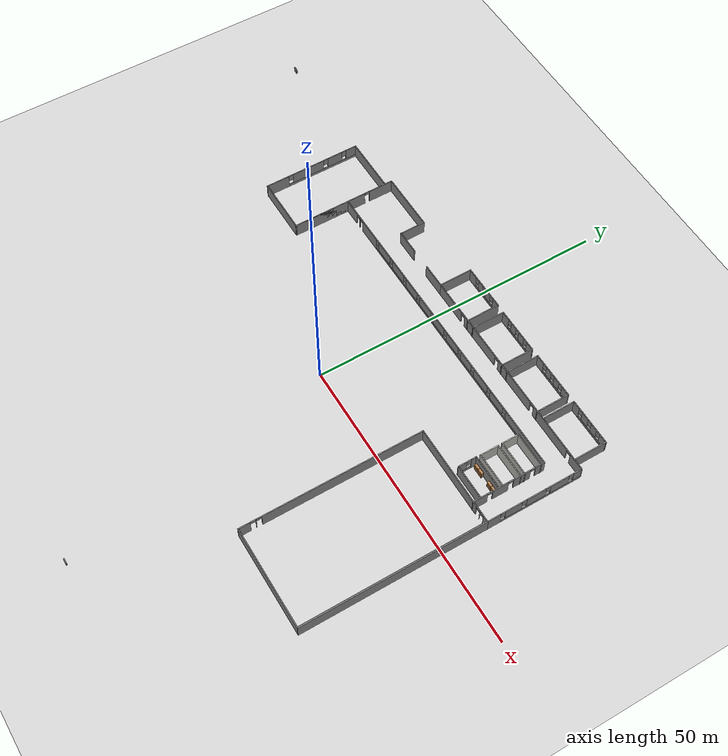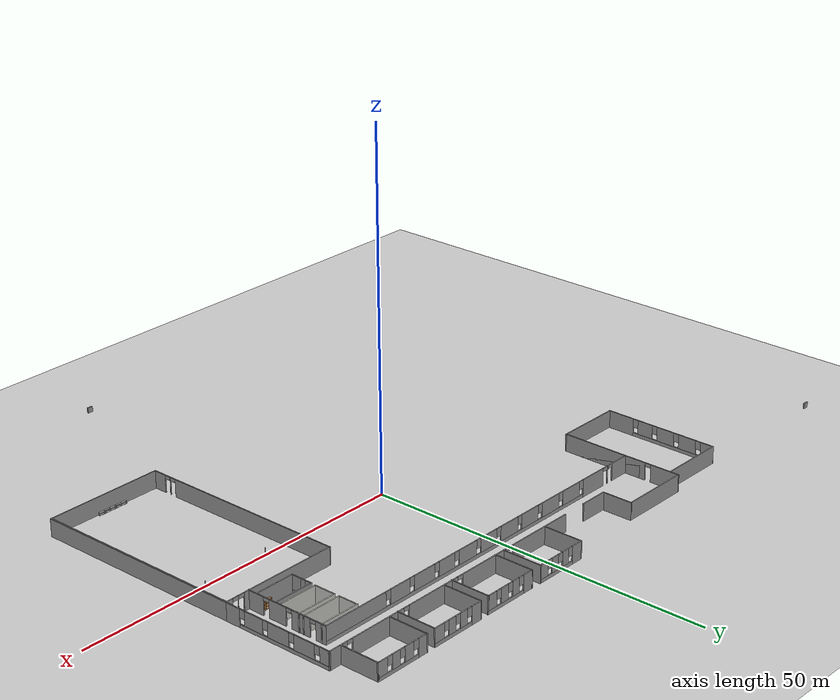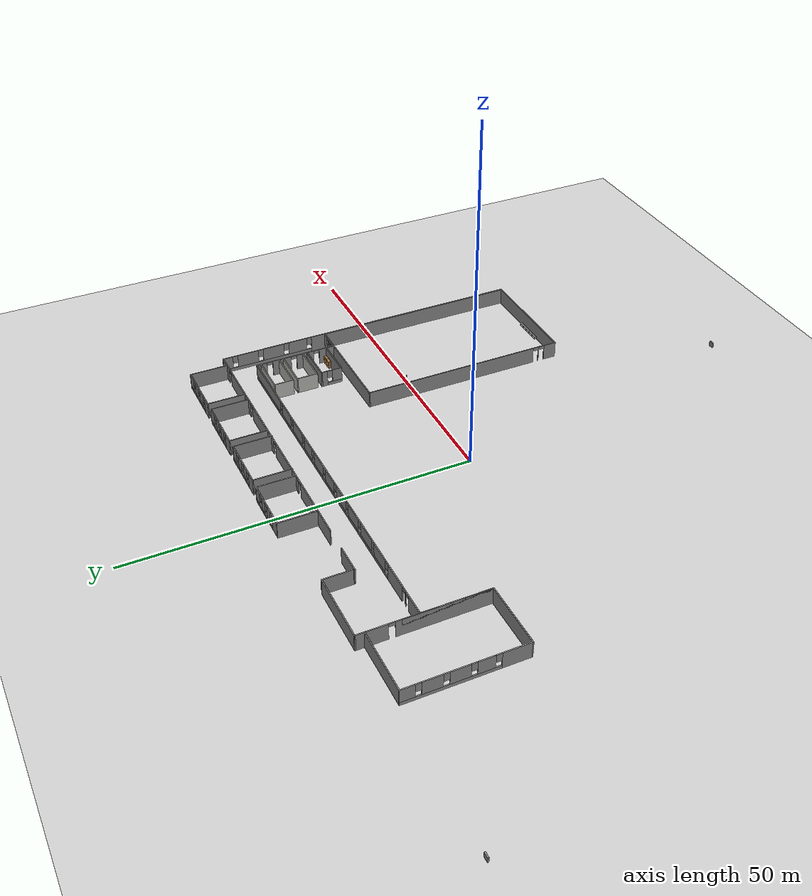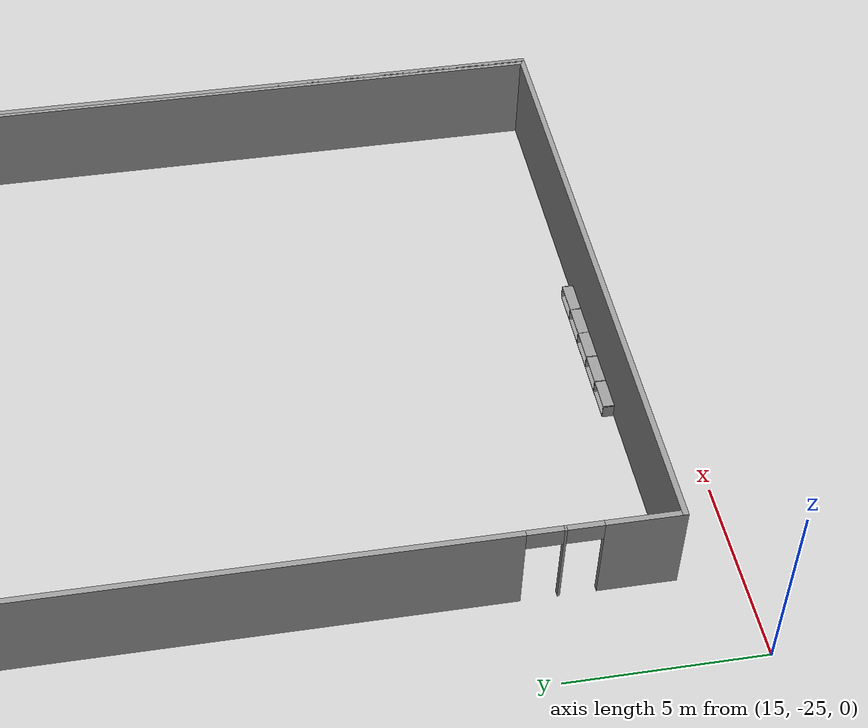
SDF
<sdf version="1.6">
 <world name="default">
  <model name="ground_plane">
   <static>1</static>
   <link name="link">
    <collision name="collision">
     <geometry><plane><normal>0 0 1</normal><size>100 100</size></plane></geometry>
     <surface>
      <contact><collide_bitmask>65535</collide_bitmask></contact>
      <friction><ode><mu>100</mu><mu2>50</mu2></ode></friction>
     </surface>
    </collision>
    <visual name="visual">
     <cast_shadows>0</cast_shadows>
     <geometry><plane><normal>0 0 1</normal><size>100 100</size></plane></geometry>
     <material>
      <script><uri>file://media/materials/scripts/gazebo.material</uri><name>Gazebo/Grey</name></script>
     </material>
    </visual>
   </link>
  </model>
  <light name="sun" type="directional">
   <pose>0 0 10 0 -0 0</pose>
   <diffuse>0.8 0.8 0.8 1</diffuse>
   <specular>0.2 0.2 0.2 1</specular>
   <attenuation>
    <range>1000</range>
    <constant>0.9</constant>
    <linear>0.01</linear>
    <quadratic>0.001</quadratic>
   </attenuation>
   <direction>-0.5 0.1 -0.9</direction>
  </light>
  <model name="firstFloor">
   <pose>-0.116512 3.07366 0 0 -0 0</pose>
   <link name="Wall_0">
    <pose>17.6408 -10.9848 0 0 0 -1.5708</pose>
    <visual name="Wall_0_Visual_0">
     <pose>-1.92288 0 1.25 0 -0 0</pose>
     <geometry><box><size>27.1542 0.15 2.5</size></box></geometry>
     <material>
      <script><uri>file://media/materials/scripts/gazebo.material</uri><name>Gazebo/Grey</name></script>
      <ambient>1 1 1 1</ambient>
     </material>
     <meta><layer>0</layer></meta>
    </visual>
    <collision name="Wall_0_Collision_0">
     <geometry><box><size>27.1542 0.15 2.5</size></box></geometry>
     <pose>-1.92288 0 1.25 0 -0 0</pose>
    </collision>
    <visual name="Wall_0_Visual_1">
     <pose>12.5857 0 1.25 0 -0 0</pose>
     <geometry><box><size>0.062944 0.15 2.5</size></box></geometry>
     <material>
      <script><uri>file://media/materials/scripts/gazebo.material</uri><name>Gazebo/Grey</name></script>
      <ambient>1 1 1 1</ambient>
     </material>
     <meta><layer>0</layer></meta>
    </visual>
    <collision name="Wall_0_Collision_1">
     <geometry><box><size>0.062944 0.15 2.5</size></box></geometry>
     <pose>12.5857 0 1.25 0 -0 0</pose>
    </collision>
    <visual name="Wall_0_Visual_2">
     <pose>14.5086 0 1.25 0 -0 0</pose>
     <geometry><box><size>1.98281 0.15 2.5</size></box></geometry>
     <material>
      <script><uri>file://media/materials/scripts/gazebo.material</uri><name>Gazebo/Grey</name></script>
      <ambient>1 1 1 1</ambient>
     </material>
     <meta><layer>0</layer></meta>
    </visual>
    <collision name="Wall_0_Collision_2">
     <geometry><box><size>1.98281 0.15 2.5</size></box></geometry>
     <pose>14.5086 0 1.25 0 -0 0</pose>
    </collision>
    <visual name="Wall_0_Visual_3">
     <pose>12.1042 0 2.25 0 -0 0</pose>
     <geometry><box><size>0.9 0.15 0.5</size></box></geometry>
     <material>
      <script><uri>file://media/materials/scripts/gazebo.material</uri><name>Gazebo/Grey</name></script>
      <ambient>1 1 1 1</ambient>
     </material>
     <meta><layer>0</layer></meta>
    </visual>
    <collision name="Wall_0_Collision_3">
     <geometry><box><size>0.9 0.15 0.5</size></box></geometry>
     <pose>12.1042 0 2.25 0 -0 0</pose>
    </collision>
    <visual name="Wall_0_Visual_4">
     <pose>13.0672 0 2.25 0 -0 0</pose>
     <geometry><box><size>0.9 0.15 0.5</size></box></geometry>
     <material>
      <script><uri>file://media/materials/scripts/gazebo.material</uri><name>Gazebo/Grey</name></script>
      <ambient>1 1 1 1</ambient>
     </material>
     <meta><layer>0</layer></meta>
    </visual>
    <collision name="Wall_0_Collision_4">
     <geometry><box><size>0.9 0.15 0.5</size></box></geometry>
     <pose>13.0672 0 2.25 0 -0 0</pose>
    </collision>
   </link>
   <link name="Wall_1">
    <collision name="Wall_1_Collision">
     <geometry><box><size>17.25 0.15 2.5</size></box></geometry>
     <pose>0 0 1.25 0 -0 0</pose>
    </collision>
    <visual name="Wall_1_Visual">
     <pose>0 0 1.25 0 -0 0</pose>
     <geometry><box><size>17.25 0.15 2.5</size></box></geometry>
     <material>
      <script><uri>file://media/materials/scripts/gazebo.material</uri><name>Gazebo/Grey</name></script>
      <ambient>1 1 1 1</ambient>
     </material>
     <meta><layer>0</layer></meta>
    </visual>
    <pose>26.1908 -26.4098 0 0 -0 0</pose>
   </link>
   <link name="Wall_15">
    <pose>2.99839 16.757 0 0 -0 0</pose>
    <visual name="Wall_15_Visual_0">
     <pose>-26.7456 0 1.25 0 -0 0</pose>
     <geometry><box><size>3.00874 0.15 2.5</size></box></geometry>
     <material>
      <script><uri>file://media/materials/scripts/gazebo.material</uri><name>Gazebo/Grey</name></script>
      <ambient>1 1 1 1</ambient>
     </material>
     <meta><layer>0</layer></meta>
    </visual>
    <collision name="Wall_15_Collision_0">
     <geometry><box><size>3.00874 0.15 2.5</size></box></geometry>
     <pose>-26.7456 0 1.25 0 -0 0</pose>
    </collision>
    <visual name="Wall_15_Visual_1">
     <pose>-24.2997 0 1.25 0 -0 0</pose>
     <geometry><box><size>0.083156 0.15 2.5</size></box></geometry>
     <material>
      <script><uri>file://media/materials/scripts/gazebo.material</uri><name>Gazebo/Grey</name></script>
      <ambient>1 1 1 1</ambient>
     </material>
     <meta><layer>0</layer></meta>
    </visual>
    <collision name="Wall_15_Collision_1">
     <geometry><box><size>0.083156 0.15 2.5</size></box></geometry>
     <pose>-24.2997 0 1.25 0 -0 0</pose>
    </collision>
    <visual name="Wall_15_Visual_2">
     <pose>-21.2466 0 1.25 0 -0 0</pose>
     <geometry><box><size>4.22309 0.15 2.5</size></box></geometry>
     <material>
      <script><uri>file://media/materials/scripts/gazebo.material</uri><name>Gazebo/Grey</name></script>
      <ambient>1 1 1 1</ambient>
     </material>
     <meta><layer>0</layer></meta>
    </visual>
    <collision name="Wall_15_Collision_2">
     <geometry><box><size>4.22309 0.15 2.5</size></box></geometry>
     <pose>-21.2466 0 1.25 0 -0 0</pose>
    </collision>
    <visual name="Wall_15_Visual_3">
     <pose>4.55749 0 0.25 0 -0 0</pose>
     <geometry><box><size>47.385 0.15 0.5</size></box></geometry>
     <material>
      <script><uri>file://media/materials/scripts/gazebo.material</uri><name>Gazebo/Grey</name></script>
      <ambient>1 1 1 1</ambient>
     </material>
     <meta><layer>0</layer></meta>
    </visual>
    <collision name="Wall_15_Collision_3">
     <geometry><box><size>47.385 0.15 0.5</size></box></geometry>
     <pose>4.55749 0 0.25 0 -0 0</pose>
    </collision>
    <visual name="Wall_15_Visual_4">
     <pose>-16.6507 0 1.5 0 -0 0</pose>
     <geometry><box><size>3.36858 0.15 2</size></box></geometry>
     <material>
      <script><uri>file://media/materials/scripts/gazebo.material</uri><name>Gazebo/Grey</name></script>
      <ambient>1 1 1 1</ambient>
     </material>
     <meta><layer>0</layer></meta>
    </visual>
    <collision name="Wall_15_Collision_4">
     <geometry><box><size>3.36858 0.15 2</size></box></geometry>
     <pose>-16.6507 0 1.5 0 -0 0</pose>
    </collision>
    <visual name="Wall_15_Visual_5">
     <pose>-12.4625 0 1.5 0 -0 0</pose>
     <geometry><box><size>3.40791 0.15 2</size></box></geometry>
     <material>
      <script><uri>file://media/materials/scripts/gazebo.material</uri><name>Gazebo/Grey</name></script>
      <ambient>1 1 1 1</ambient>
     </material>
     <meta><layer>0</layer></meta>
    </visual>
    <collision name="Wall_15_Collision_5">
     <geometry><box><size>3.40791 0.15 2</size></box></geometry>
     <pose>-12.4625 0 1.5 0 -0 0</pose>
    </collision>
    <visual name="Wall_15_Visual_6">
     <pose>-8.34568 0 1.5 0 -0 0</pose>
     <geometry><box><size>3.2257 0.15 2</size></box></geometry>
     <material>
      <script><uri>file://media/materials/scripts/gazebo.material</uri><name>Gazebo/Grey</name></script>
      <ambient>1 1 1 1</ambient>
     </material>
     <meta><layer>0</layer></meta>
    </visual>
    <collision name="Wall_15_Collision_6">
     <geometry><box><size>3.2257 0.15 2</size></box></geometry>
     <pose>-8.34568 0 1.5 0 -0 0</pose>
    </collision>
    <visual name="Wall_15_Visual_7">
     <pose>-4.31076 0 1.5 0 -0 0</pose>
     <geometry><box><size>3.24413 0.15 2</size></box></geometry>
     <material>
      <script><uri>file://media/materials/scripts/gazebo.material</uri><name>Gazebo/Grey</name></script>
      <ambient>1 1 1 1</ambient>
     </material>
     <meta><layer>0</layer></meta>
    </visual>
    <collision name="Wall_15_Collision_7">
     <geometry><box><size>3.24413 0.15 2</size></box></geometry>
     <pose>-4.31076 0 1.5 0 -0 0</pose>
    </collision>
    <visual name="Wall_15_Visual_8">
     <pose>-0.385574 0 1.5 0 -0 0</pose>
     <geometry><box><size>3.00624 0.15 2</size></box></geometry>
     <material>
      <script><uri>file://media/materials/scripts/gazebo.material</uri><name>Gazebo/Grey</name></script>
      <ambient>1 1 1 1</ambient>
     </material>
     <meta><layer>0</layer></meta>
    </visual>
    <collision name="Wall_15_Collision_8">
     <geometry><box><size>3.00624 0.15 2</size></box></geometry>
     <pose>-0.385574 0 1.5 0 -0 0</pose>
    </collision>
    <visual name="Wall_15_Visual_9">
     <pose>3.53961 0 1.5 0 -0 0</pose>
     <geometry><box><size>3.24413 0.15 2</size></box></geometry>
     <material>
      <script><uri>file://media/materials/scripts/gazebo.material</uri><name>Gazebo/Grey</name></script>
      <ambient>1 1 1 1</ambient>
     </material>
     <meta><layer>0</layer></meta>
    </visual>
    <collision name="Wall_15_Collision_9">
     <geometry><box><size>3.24413 0.15 2</size></box></geometry>
     <pose>3.53961 0 1.5 0 -0 0</pose>
    </collision>
    <visual name="Wall_15_Visual_10">
     <pose>7.39046 0 1.5 0 -0 0</pose>
     <geometry><box><size>2.85756 0.15 2</size></box></geometry>
     <material>
      <script><uri>file://media/materials/scripts/gazebo.material</uri><name>Gazebo/Grey</name></script>
      <ambient>1 1 1 1</ambient>
     </material>
     <meta><layer>0</layer></meta>
    </visual>
    <collision name="Wall_15_Collision_10">
     <geometry><box><size>2.85756 0.15 2</size></box></geometry>
     <pose>7.39046 0 1.5 0 -0 0</pose>
    </collision>
    <visual name="Wall_15_Visual_11">
     <pose>11.4197 0 1.5 0 -0 0</pose>
     <geometry><box><size>3.60097 0.15 2</size></box></geometry>
     <material>
      <script><uri>file://media/materials/scripts/gazebo.material</uri><name>Gazebo/Grey</name></script>
      <ambient>1 1 1 1</ambient>
     </material>
     <meta><layer>0</layer></meta>
    </visual>
    <collision name="Wall_15_Collision_11">
     <geometry><box><size>3.60097 0.15 2</size></box></geometry>
     <pose>11.4197 0 1.5 0 -0 0</pose>
    </collision>
    <visual name="Wall_15_Visual_12">
     <pose>15.7166 0 1.5 0 -0 0</pose>
     <geometry><box><size>3.39282 0.15 2</size></box></geometry>
     <material>
      <script><uri>file://media/materials/scripts/gazebo.material</uri><name>Gazebo/Grey</name></script>
      <ambient>1 1 1 1</ambient>
     </material>
     <meta><layer>0</layer></meta>
    </visual>
    <collision name="Wall_15_Collision_12">
     <geometry><box><size>3.39282 0.15 2</size></box></geometry>
     <pose>15.7166 0 1.5 0 -0 0</pose>
    </collision>
    <visual name="Wall_15_Visual_13">
     <pose>23.2315 0 1.5 0 -0 0</pose>
     <geometry><box><size>10.037 0.15 2</size></box></geometry>
     <material>
      <script><uri>file://media/materials/scripts/gazebo.material</uri><name>Gazebo/Grey</name></script>
      <ambient>1 1 1 1</ambient>
     </material>
     <meta><layer>0</layer></meta>
    </visual>
    <collision name="Wall_15_Collision_13">
     <geometry><box><size>10.037 0.15 2</size></box></geometry>
     <pose>23.2315 0 1.5 0 -0 0</pose>
    </collision>
    <visual name="Wall_15_Visual_14">
     <pose>-18.735 0 1.9 0 -0 0</pose>
     <geometry><box><size>0.8 0.15 1.2</size></box></geometry>
     <material>
      <script><uri>file://media/materials/scripts/gazebo.material</uri><name>Gazebo/Grey</name></script>
      <ambient>1 1 1 1</ambient>
     </material>
     <meta><layer>0</layer></meta>
    </visual>
    <collision name="Wall_15_Collision_14">
     <geometry><box><size>0.8 0.15 1.2</size></box></geometry>
     <pose>-18.735 0 1.9 0 -0 0</pose>
    </collision>
    <visual name="Wall_15_Visual_15">
     <pose>-14.5664 0 1.9 0 -0 0</pose>
     <geometry><box><size>0.8 0.15 1.2</size></box></geometry>
     <material>
      <script><uri>file://media/materials/scripts/gazebo.material</uri><name>Gazebo/Grey</name></script>
      <ambient>1 1 1 1</ambient>
     </material>
     <meta><layer>0</layer></meta>
    </visual>
    <collision name="Wall_15_Collision_15">
     <geometry><box><size>0.8 0.15 1.2</size></box></geometry>
     <pose>-14.5664 0 1.9 0 -0 0</pose>
    </collision>
    <visual name="Wall_15_Visual_16">
     <pose>-10.3585 0 1.9 0 -0 0</pose>
     <geometry><box><size>0.8 0.15 1.2</size></box></geometry>
     <material>
      <script><uri>file://media/materials/scripts/gazebo.material</uri><name>Gazebo/Grey</name></script>
      <ambient>1 1 1 1</ambient>
     </material>
     <meta><layer>0</layer></meta>
    </visual>
    <collision name="Wall_15_Collision_16">
     <geometry><box><size>0.8 0.15 1.2</size></box></geometry>
     <pose>-10.3585 0 1.9 0 -0 0</pose>
    </collision>
    <visual name="Wall_15_Visual_17">
     <pose>-6.33283 0 1.9 0 -0 0</pose>
     <geometry><box><size>0.8 0.15 1.2</size></box></geometry>
     <material>
      <script><uri>file://media/materials/scripts/gazebo.material</uri><name>Gazebo/Grey</name></script>
      <ambient>1 1 1 1</ambient>
     </material>
     <meta><layer>0</layer></meta>
    </visual>
    <collision name="Wall_15_Collision_17">
     <geometry><box><size>0.8 0.15 1.2</size></box></geometry>
     <pose>-6.33283 0 1.9 0 -0 0</pose>
    </collision>
    <visual name="Wall_15_Visual_18">
     <pose>-2.2887 0 1.9 0 -0 0</pose>
     <geometry><box><size>0.8 0.15 1.2</size></box></geometry>
     <material>
      <script><uri>file://media/materials/scripts/gazebo.material</uri><name>Gazebo/Grey</name></script>
      <ambient>1 1 1 1</ambient>
     </material>
     <meta><layer>0</layer></meta>
    </visual>
    <collision name="Wall_15_Collision_18">
     <geometry><box><size>0.8 0.15 1.2</size></box></geometry>
     <pose>-2.2887 0 1.9 0 -0 0</pose>
    </collision>
    <visual name="Wall_15_Visual_19">
     <pose>1.51755 0 1.9 0 -0 0</pose>
     <geometry><box><size>0.8 0.15 1.2</size></box></geometry>
     <material>
      <script><uri>file://media/materials/scripts/gazebo.material</uri><name>Gazebo/Grey</name></script>
      <ambient>1 1 1 1</ambient>
     </material>
     <meta><layer>0</layer></meta>
    </visual>
    <collision name="Wall_15_Collision_19">
     <geometry><box><size>0.8 0.15 1.2</size></box></geometry>
     <pose>1.51755 0 1.9 0 -0 0</pose>
    </collision>
    <visual name="Wall_15_Visual_20">
     <pose>5.56168 0 1.9 0 -0 0</pose>
     <geometry><box><size>0.8 0.15 1.2</size></box></geometry>
     <material>
      <script><uri>file://media/materials/scripts/gazebo.material</uri><name>Gazebo/Grey</name></script>
      <ambient>1 1 1 1</ambient>
     </material>
     <meta><layer>0</layer></meta>
    </visual>
    <collision name="Wall_15_Collision_20">
     <geometry><box><size>0.8 0.15 1.2</size></box></geometry>
     <pose>5.56168 0 1.9 0 -0 0</pose>
    </collision>
    <visual name="Wall_15_Visual_21">
     <pose>9.21925 0 1.9 0 -0 0</pose>
     <geometry><box><size>0.8 0.15 1.2</size></box></geometry>
     <material>
      <script><uri>file://media/materials/scripts/gazebo.material</uri><name>Gazebo/Grey</name></script>
      <ambient>1 1 1 1</ambient>
     </material>
     <meta><layer>0</layer></meta>
    </visual>
    <collision name="Wall_15_Collision_21">
     <geometry><box><size>0.8 0.15 1.2</size></box></geometry>
     <pose>9.21925 0 1.9 0 -0 0</pose>
    </collision>
    <visual name="Wall_15_Visual_22">
     <pose>13.6202 0 1.9 0 -0 0</pose>
     <geometry><box><size>0.8 0.15 1.2</size></box></geometry>
     <material>
      <script><uri>file://media/materials/scripts/gazebo.material</uri><name>Gazebo/Grey</name></script>
      <ambient>1 1 1 1</ambient>
     </material>
     <meta><layer>0</layer></meta>
    </visual>
    <collision name="Wall_15_Collision_22">
     <geometry><box><size>0.8 0.15 1.2</size></box></geometry>
     <pose>13.6202 0 1.9 0 -0 0</pose>
    </collision>
    <visual name="Wall_15_Visual_23">
     <pose>17.813 0 1.9 0 -0 0</pose>
     <geometry><box><size>0.8 0.15 1.2</size></box></geometry>
     <material>
      <script><uri>file://media/materials/scripts/gazebo.material</uri><name>Gazebo/Grey</name></script>
      <ambient>1 1 1 1</ambient>
     </material>
     <meta><layer>0</layer></meta>
    </visual>
    <collision name="Wall_15_Collision_23">
     <geometry><box><size>0.8 0.15 1.2</size></box></geometry>
     <pose>17.813 0 1.9 0 -0 0</pose>
    </collision>
    <visual name="Wall_15_Visual_24">
     <pose>-24.7913 0 2.25 0 -0 0</pose>
     <geometry><box><size>0.9 0.15 0.5</size></box></geometry>
     <material>
      <script><uri>file://media/materials/scripts/gazebo.material</uri><name>Gazebo/Grey</name></script>
      <ambient>1 1 1 1</ambient>
     </material>
     <meta><layer>0</layer></meta>
    </visual>
    <collision name="Wall_15_Collision_24">
     <geometry><box><size>0.9 0.15 0.5</size></box></geometry>
     <pose>-24.7913 0 2.25 0 -0 0</pose>
    </collision>
    <visual name="Wall_15_Visual_25">
     <pose>-23.8081 0 2.25 0 -0 0</pose>
     <geometry><box><size>0.9 0.15 0.5</size></box></geometry>
     <material>
      <script><uri>file://media/materials/scripts/gazebo.material</uri><name>Gazebo/Grey</name></script>
      <ambient>1 1 1 1</ambient>
     </material>
     <meta><layer>0</layer></meta>
    </visual>
    <collision name="Wall_15_Collision_25">
     <geometry><box><size>0.9 0.15 0.5</size></box></geometry>
     <pose>-23.8081 0 2.25 0 -0 0</pose>
    </collision>
   </link>
   <link name="Wall_16">
    <pose>31.1734 10.582 0 0 0 -1.5708</pose>
    <visual name="Wall_16_Visual_0">
     <pose>-5.43447 0 1.25 0 -0 0</pose>
     <geometry><box><size>1.63106 0.15 2.5</size></box></geometry>
     <material>
      <script><uri>file://media/materials/scripts/gazebo.material</uri><name>Gazebo/Grey</name></script>
      <ambient>1 1 1 1</ambient>
     </material>
     <meta><layer>0</layer></meta>
    </visual>
    <collision name="Wall_16_Collision_0">
     <geometry><box><size>1.63106 0.15 2.5</size></box></geometry>
     <pose>-5.43447 0 1.25 0 -0 0</pose>
    </collision>
    <visual name="Wall_16_Visual_1">
     <pose>-2.26346 0 1.25 0 -0 0</pose>
     <geometry><box><size>2.91096 0.15 2.5</size></box></geometry>
     <material>
      <script><uri>file://media/materials/scripts/gazebo.material</uri><name>Gazebo/Grey</name></script>
      <ambient>1 1 1 1</ambient>
     </material>
     <meta><layer>0</layer></meta>
    </visual>
    <collision name="Wall_16_Collision_1">
     <geometry><box><size>2.91096 0.15 2.5</size></box></geometry>
     <pose>-2.26346 0 1.25 0 -0 0</pose>
    </collision>
    <visual name="Wall_16_Visual_2">
     <pose>1.45677 0 1.25 0 -0 0</pose>
     <geometry><box><size>2.72949 0.15 2.5</size></box></geometry>
     <material>
      <script><uri>file://media/materials/scripts/gazebo.material</uri><name>Gazebo/Grey</name></script>
      <ambient>1 1 1 1</ambient>
     </material>
     <meta><layer>0</layer></meta>
    </visual>
    <collision name="Wall_16_Collision_2">
     <geometry><box><size>2.72949 0.15 2.5</size></box></geometry>
     <pose>1.45677 0 1.25 0 -0 0</pose>
    </collision>
    <visual name="Wall_16_Visual_3">
     <pose>4.98576 0 1.25 0 -0 0</pose>
     <geometry><box><size>2.52848 0.15 2.5</size></box></geometry>
     <material>
      <script><uri>file://media/materials/scripts/gazebo.material</uri><name>Gazebo/Grey</name></script>
      <ambient>1 1 1 1</ambient>
     </material>
     <meta><layer>0</layer></meta>
    </visual>
    <collision name="Wall_16_Collision_3">
     <geometry><box><size>2.52848 0.15 2.5</size></box></geometry>
     <pose>4.98576 0 1.25 0 -0 0</pose>
    </collision>
    <visual name="Wall_16_Visual_4">
     <pose>-4.16894 0 2.25 0 -0 0</pose>
     <geometry><box><size>0.9 0.15 0.5</size></box></geometry>
     <material>
      <script><uri>file://media/materials/scripts/gazebo.material</uri><name>Gazebo/Grey</name></script>
      <ambient>1 1 1 1</ambient>
     </material>
     <meta><layer>0</layer></meta>
    </visual>
    <collision name="Wall_16_Collision_4">
     <geometry><box><size>0.9 0.15 0.5</size></box></geometry>
     <pose>-4.16894 0 2.25 0 -0 0</pose>
    </collision>
    <visual name="Wall_16_Visual_5">
     <pose>-0.357975 0 2.25 0 -0 0</pose>
     <geometry><box><size>0.9 0.15 0.5</size></box></geometry>
     <material>
      <script><uri>file://media/materials/scripts/gazebo.material</uri><name>Gazebo/Grey</name></script>
      <ambient>1 1 1 1</ambient>
     </material>
     <meta><layer>0</layer></meta>
    </visual>
    <collision name="Wall_16_Collision_5">
     <geometry><box><size>0.9 0.15 0.5</size></box></geometry>
     <pose>-0.357975 0 2.25 0 -0 0</pose>
    </collision>
    <visual name="Wall_16_Visual_6">
     <pose>3.27151 0 2.25 0 -0 0</pose>
     <geometry><box><size>0.9 0.15 0.5</size></box></geometry>
     <material>
      <script><uri>file://media/materials/scripts/gazebo.material</uri><name>Gazebo/Grey</name></script>
      <ambient>1 1 1 1</ambient>
     </material>
     <meta><layer>0</layer></meta>
    </visual>
    <collision name="Wall_16_Collision_6">
     <geometry><box><size>0.9 0.15 0.5</size></box></geometry>
     <pose>3.27151 0 2.25 0 -0 0</pose>
    </collision>
   </link>
   <link name="Wall_2">
    <collision name="Wall_2_Collision">
     <geometry><box><size>30.75 0.15 2.5</size></box></geometry>
     <pose>0 0 1.25 0 -0 0</pose>
    </collision>
    <visual name="Wall_2_Visual">
     <pose>0 0 1.25 0 -0 0</pose>
     <geometry><box><size>30.75 0.15 2.5</size></box></geometry>
     <material>
      <script><uri>file://media/materials/scripts/gazebo.material</uri><name>Gazebo/Grey</name></script>
      <ambient>1 1 1 1</ambient>
     </material>
     <meta><layer>0</layer></meta>
    </visual>
    <pose>34.7408 -11.1098 0 0 -0 1.5708</pose>
   </link>
   <link name="Wall_20">
    <collision name="Wall_20_Collision">
     <geometry><box><size>6 0.15 2.5</size></box></geometry>
     <pose>0 0 1.25 0 -0 0</pose>
    </collision>
    <visual name="Wall_20_Visual">
     <pose>0 0 1.25 0 -0 0</pose>
     <geometry><box><size>6 0.15 2.5</size></box></geometry>
     <material>
      <script><uri>file://media/materials/scripts/gazebo.material</uri><name>Gazebo/CeilingTiled</name></script>
      <ambient>1 1 1 1</ambient>
     </material>
     <meta><layer>0</layer></meta>
    </visual>
    <pose>28.2901 16.1378 0 0 -0 3.14159</pose>
   </link>
   <link name="Wall_21">
    <collision name="Wall_21_Collision">
     <geometry><box><size>3 0.15 2.5</size></box></geometry>
     <pose>0 0 1.25 0 -0 0</pose>
    </collision>
    <visual name="Wall_21_Visual">
     <pose>0 0 1.25 0 -0 0</pose>
     <geometry><box><size>3 0.15 2.5</size></box></geometry>
     <material>
      <script><uri>file://media/materials/scripts/gazebo.material</uri><name>Gazebo/CeilingTiled</name></script>
      <ambient>1 1 1 1</ambient>
     </material>
     <meta><layer>0</layer></meta>
    </visual>
    <pose>25.3651 14.7128 0 0 0 -1.5708</pose>
   </link>
   <link name="Wall_22">
    <collision name="Wall_22_Collision">
     <geometry><box><size>6 0.15 2.5</size></box></geometry>
     <pose>0 0 1.25 0 -0 0</pose>
    </collision>
    <visual name="Wall_22_Visual">
     <pose>0 0 1.25 0 -0 0</pose>
     <geometry><box><size>6 0.15 2.5</size></box></geometry>
     <material>
      <script><uri>file://media/materials/scripts/gazebo.material</uri><name>Gazebo/CeilingTiled</name></script>
      <ambient>1 1 1 1</ambient>
     </material>
     <meta><layer>0</layer></meta>
    </visual>
    <pose>28.2901 13.2878 0 0 -0 0</pose>
   </link>
   <link name="Wall_24">
    <collision name="Wall_24_Collision">
     <geometry><box><size>6 0.15 2.5</size></box></geometry>
     <pose>0 0 1.25 0 -0 0</pose>
    </collision>
    <visual name="Wall_24_Visual">
     <pose>0 0 1.25 0 -0 0</pose>
     <geometry><box><size>6 0.15 2.5</size></box></geometry>
     <material>
      <script><uri>file://media/materials/scripts/gazebo.material</uri><name>Gazebo/CeilingTiled</name></script>
      <ambient>1 1 1 1</ambient>
     </material>
     <meta><layer>0</layer></meta>
    </visual>
    <pose>28.3012 12.5835 0 0 -0 3.14159</pose>
   </link>
   <link name="Wall_25">
    <collision name="Wall_25_Collision">
     <geometry><box><size>3.25 0.15 2.5</size></box></geometry>
     <pose>0 0 1.25 0 -0 0</pose>
    </collision>
    <visual name="Wall_25_Visual">
     <pose>0 0 1.25 0 -0 0</pose>
     <geometry><box><size>3.25 0.15 2.5</size></box></geometry>
     <material>
      <script><uri>file://media/materials/scripts/gazebo.material</uri><name>Gazebo/CeilingTiled</name></script>
      <ambient>1 1 1 1</ambient>
     </material>
     <meta><layer>0</layer></meta>
    </visual>
    <pose>25.3762 11.0335 0 0 0 -1.5708</pose>
   </link>
   <link name="Wall_26">
    <collision name="Wall_26_Collision">
     <geometry><box><size>5.75 0.15 2.5</size></box></geometry>
     <pose>0 0 1.25 0 -0 0</pose>
    </collision>
    <visual name="Wall_26_Visual">
     <pose>0 0 1.25 0 -0 0</pose>
     <geometry><box><size>5.75 0.15 2.5</size></box></geometry>
     <material>
      <script><uri>file://media/materials/scripts/gazebo.material</uri><name>Gazebo/CeilingTiled</name></script>
      <ambient>1 1 1 1</ambient>
     </material>
     <meta><layer>0</layer></meta>
    </visual>
    <pose>28.1762 9.48348 0 0 -0 0</pose>
   </link>
   <link name="Wall_28">
    <collision name="Wall_28_Collision">
     <geometry><box><size>6 0.15 2.5</size></box></geometry>
     <pose>0 0 1.25 0 -0 0</pose>
    </collision>
    <visual name="Wall_28_Visual">
     <pose>0 0 1.25 0 -0 0</pose>
     <geometry><box><size>6 0.15 2.5</size></box></geometry>
     <material>
      <script><uri>file://media/materials/scripts/gazebo.material</uri><name>Gazebo/Grey</name></script>
      <ambient>1 1 1 1</ambient>
     </material>
     <meta><layer>0</layer></meta>
    </visual>
    <pose>28.2321 8.78663 0 0 -0 3.14159</pose>
   </link>
   <link name="Wall_29">
    <pose>25.3071 7.23663 0 0 0 -1.5708</pose>
    <visual name="Wall_29_Visual_0">
     <pose>-1.14911 0 1.25 0 -0 0</pose>
     <geometry><box><size>0.951772 0.15 2.5</size></box></geometry>
     <material>
      <script><uri>file://media/materials/scripts/gazebo.material</uri><name>Gazebo/Grey</name></script>
      <ambient>1 1 1 1</ambient>
     </material>
     <meta><layer>0</layer></meta>
    </visual>
    <collision name="Wall_29_Collision_0">
     <geometry><box><size>0.951772 0.15 2.5</size></box></geometry>
     <pose>-1.14911 0 1.25 0 -0 0</pose>
    </collision>
    <visual name="Wall_29_Visual_1">
     <pose>0.475886 0 0.25 0 -0 0</pose>
     <geometry><box><size>2.29823 0.15 0.5</size></box></geometry>
     <material>
      <script><uri>file://media/materials/scripts/gazebo.material</uri><name>Gazebo/Grey</name></script>
      <ambient>1 1 1 1</ambient>
     </material>
     <meta><layer>0</layer></meta>
    </visual>
    <collision name="Wall_29_Collision_1">
     <geometry><box><size>2.29823 0.15 0.5</size></box></geometry>
     <pose>0.475886 0 0.25 0 -0 0</pose>
    </collision>
    <visual name="Wall_29_Visual_2">
     <pose>0.875886 0 1.5 0 -0 0</pose>
     <geometry><box><size>1.49823 0.15 2</size></box></geometry>
     <material>
      <script><uri>file://media/materials/scripts/gazebo.material</uri><name>Gazebo/Grey</name></script>
      <ambient>1 1 1 1</ambient>
     </material>
     <meta><layer>0</layer></meta>
    </visual>
    <collision name="Wall_29_Collision_2">
     <geometry><box><size>1.49823 0.15 2</size></box></geometry>
     <pose>0.875886 0 1.5 0 -0 0</pose>
    </collision>
    <visual name="Wall_29_Visual_3">
     <pose>-0.273228 0 1.9 0 -0 0</pose>
     <geometry><box><size>0.8 0.15 1.2</size></box></geometry>
     <material>
      <script><uri>file://media/materials/scripts/gazebo.material</uri><name>Gazebo/Grey</name></script>
      <ambient>1 1 1 1</ambient>
     </material>
     <meta><layer>0</layer></meta>
    </visual>
    <collision name="Wall_29_Collision_3">
     <geometry><box><size>0.8 0.15 1.2</size></box></geometry>
     <pose>-0.273228 0 1.9 0 -0 0</pose>
    </collision>
   </link>
   <link name="Wall_30">
    <collision name="Wall_30_Collision">
     <geometry><box><size>6 0.15 2.5</size></box></geometry>
     <pose>0 0 1.25 0 -0 0</pose>
    </collision>
    <visual name="Wall_30_Visual">
     <pose>0 0 1.25 0 -0 0</pose>
     <geometry><box><size>6 0.15 2.5</size></box></geometry>
     <material>
      <script><uri>file://media/materials/scripts/gazebo.material</uri><name>Gazebo/Grey</name></script>
      <ambient>1 1 1 1</ambient>
     </material>
     <meta><layer>0</layer></meta>
    </visual>
    <pose>28.2321 5.68663 0 0 -0 0</pose>
   </link>
   <link name="Wall_32">
    <pose>15.7968 20.7947 0 0 -0 3.14159</pose>
    <visual name="Wall_32_Visual_0">
     <pose>-17.6843 0 1.25 0 -0 0</pose>
     <geometry><box><size>2.88139 0.15 2.5</size></box></geometry>
     <material>
      <script><uri>file://media/materials/scripts/gazebo.material</uri><name>Gazebo/Grey</name></script>
      <ambient>1 1 1 1</ambient>
     </material>
     <meta><layer>0</layer></meta>
    </visual>
    <collision name="Wall_32_Collision_0">
     <geometry><box><size>2.88139 0.15 2.5</size></box></geometry>
     <pose>-17.6843 0 1.25 0 -0 0</pose>
    </collision>
    <visual name="Wall_32_Visual_1">
     <pose>-11.0804 0 1.25 0 -0 0</pose>
     <geometry><box><size>8.52647 0.15 2.5</size></box></geometry>
     <material>
      <script><uri>file://media/materials/scripts/gazebo.material</uri><name>Gazebo/Grey</name></script>
      <ambient>1 1 1 1</ambient>
     </material>
     <meta><layer>0</layer></meta>
    </visual>
    <collision name="Wall_32_Collision_1">
     <geometry><box><size>8.52647 0.15 2.5</size></box></geometry>
     <pose>-11.0804 0 1.25 0 -0 0</pose>
    </collision>
    <visual name="Wall_32_Visual_2">
     <pose>-1.63402 0 1.25 0 -0 0</pose>
     <geometry><box><size>8.56625 0.15 2.5</size></box></geometry>
     <material>
      <script><uri>file://media/materials/scripts/gazebo.material</uri><name>Gazebo/Grey</name></script>
      <ambient>1 1 1 1</ambient>
     </material>
     <meta><layer>0</layer></meta>
    </visual>
    <collision name="Wall_32_Collision_2">
     <geometry><box><size>8.56625 0.15 2.5</size></box></geometry>
     <pose>-1.63402 0 1.25 0 -0 0</pose>
    </collision>
    <visual name="Wall_32_Visual_3">
     <pose>7.79245 0 1.25 0 -0 0</pose>
     <geometry><box><size>8.4867 0.15 2.5</size></box></geometry>
     <material>
      <script><uri>file://media/materials/scripts/gazebo.material</uri><name>Gazebo/Grey</name></script>
      <ambient>1 1 1 1</ambient>
     </material>
     <meta><layer>0</layer></meta>
    </visual>
    <collision name="Wall_32_Collision_3">
     <geometry><box><size>8.4867 0.15 2.5</size></box></geometry>
     <pose>7.79245 0 1.25 0 -0 0</pose>
    </collision>
    <visual name="Wall_32_Visual_4">
     <pose>16.0304 0 1.25 0 -0 0</pose>
     <geometry><box><size>6.1892 0.15 2.5</size></box></geometry>
     <material>
      <script><uri>file://media/materials/scripts/gazebo.material</uri><name>Gazebo/Grey</name></script>
      <ambient>1 1 1 1</ambient>
     </material>
     <meta><layer>0</layer></meta>
    </visual>
    <collision name="Wall_32_Collision_4">
     <geometry><box><size>6.1892 0.15 2.5</size></box></geometry>
     <pose>16.0304 0 1.25 0 -0 0</pose>
    </collision>
    <visual name="Wall_32_Visual_5">
     <pose>-15.7936 0 2.25 0 -0 0</pose>
     <geometry><box><size>0.9 0.15 0.5</size></box></geometry>
     <material>
      <script><uri>file://media/materials/scripts/gazebo.material</uri><name>Gazebo/Grey</name></script>
      <ambient>1 1 1 1</ambient>
     </material>
     <meta><layer>0</layer></meta>
    </visual>
    <collision name="Wall_32_Collision_5">
     <geometry><box><size>0.9 0.15 0.5</size></box></geometry>
     <pose>-15.7936 0 2.25 0 -0 0</pose>
    </collision>
    <visual name="Wall_32_Visual_6">
     <pose>-6.36714 0 2.25 0 -0 0</pose>
     <geometry><box><size>0.9 0.15 0.5</size></box></geometry>
     <material>
      <script><uri>file://media/materials/scripts/gazebo.material</uri><name>Gazebo/Grey</name></script>
      <ambient>1 1 1 1</ambient>
     </material>
     <meta><layer>0</layer></meta>
    </visual>
    <collision name="Wall_32_Collision_6">
     <geometry><box><size>0.9 0.15 0.5</size></box></geometry>
     <pose>-6.36714 0 2.25 0 -0 0</pose>
    </collision>
    <visual name="Wall_32_Visual_7">
     <pose>3.0991 0 2.25 0 -0 0</pose>
     <geometry><box><size>0.9 0.15 0.5</size></box></geometry>
     <material>
      <script><uri>file://media/materials/scripts/gazebo.material</uri><name>Gazebo/Grey</name></script>
      <ambient>1 1 1 1</ambient>
     </material>
     <meta><layer>0</layer></meta>
    </visual>
    <collision name="Wall_32_Collision_7">
     <geometry><box><size>0.9 0.15 0.5</size></box></geometry>
     <pose>3.0991 0 2.25 0 -0 0</pose>
    </collision>
    <visual name="Wall_32_Visual_8">
     <pose>12.4858 0 2.25 0 -0 0</pose>
     <geometry><box><size>0.9 0.15 0.5</size></box></geometry>
     <material>
      <script><uri>file://media/materials/scripts/gazebo.material</uri><name>Gazebo/Grey</name></script>
      <ambient>1 1 1 1</ambient>
     </material>
     <meta><layer>0</layer></meta>
    </visual>
    <collision name="Wall_32_Collision_8">
     <geometry><box><size>0.9 0.15 0.5</size></box></geometry>
     <pose>12.4858 0 2.25 0 -0 0</pose>
    </collision>
   </link>
   <link name="Wall_33">
    <collision name="Wall_33_Collision">
     <geometry><box><size>5.75 0.15 2.5</size></box></geometry>
     <pose>0 0 1.25 0 -0 0</pose>
    </collision>
    <visual name="Wall_33_Visual">
     <pose>0 0 1.25 0 -0 0</pose>
     <geometry><box><size>5.75 0.15 2.5</size></box></geometry>
     <material>
      <script><uri>file://media/materials/scripts/gazebo.material</uri><name>Gazebo/Grey</name></script>
      <ambient>1 1 1 1</ambient>
     </material>
     <meta><layer>0</layer></meta>
    </visual>
    <pose>-3.25319 23.5947 0 0 -0 1.5708</pose>
   </link>
   <link name="Wall_34">
    <pose>0.671807 26.3947 0 0 -0 0</pose>
    <visual name="Wall_34_Visual_0">
     <pose>-3.08954 0 1.25 0 -0 0</pose>
     <geometry><box><size>1.82092 0.15 2.5</size></box></geometry>
     <material>
      <script><uri>file://media/materials/scripts/gazebo.material</uri><name>Gazebo/Grey</name></script>
      <ambient>1 1 1 1</ambient>
     </material>
     <meta><layer>0</layer></meta>
    </visual>
    <collision name="Wall_34_Collision_0">
     <geometry><box><size>1.82092 0.15 2.5</size></box></geometry>
     <pose>-3.08954 0 1.25 0 -0 0</pose>
    </collision>
    <visual name="Wall_34_Visual_1">
     <pose>0.910461 0 0.25 0 -0 0</pose>
     <geometry><box><size>6.17908 0.15 0.5</size></box></geometry>
     <material>
      <script><uri>file://media/materials/scripts/gazebo.material</uri><name>Gazebo/Grey</name></script>
      <ambient>1 1 1 1</ambient>
     </material>
     <meta><layer>0</layer></meta>
    </visual>
    <collision name="Wall_34_Collision_1">
     <geometry><box><size>6.17908 0.15 0.5</size></box></geometry>
     <pose>0.910461 0 0.25 0 -0 0</pose>
    </collision>
    <visual name="Wall_34_Visual_2">
     <pose>-0.815585 0 1.5 0 -0 0</pose>
     <geometry><box><size>1.12699 0.15 2</size></box></geometry>
     <material>
      <script><uri>file://media/materials/scripts/gazebo.material</uri><name>Gazebo/Grey</name></script>
      <ambient>1 1 1 1</ambient>
     </material>
     <meta><layer>0</layer></meta>
    </visual>
    <collision name="Wall_34_Collision_2">
     <geometry><box><size>1.12699 0.15 2</size></box></geometry>
     <pose>-0.815585 0 1.5 0 -0 0</pose>
    </collision>
    <visual name="Wall_34_Visual_3">
     <pose>1.15073 0 1.5 0 -0 0</pose>
     <geometry><box><size>1.20564 0.15 2</size></box></geometry>
     <material>
      <script><uri>file://media/materials/scripts/gazebo.material</uri><name>Gazebo/Grey</name></script>
      <ambient>1 1 1 1</ambient>
     </material>
     <meta><layer>0</layer></meta>
    </visual>
    <collision name="Wall_34_Collision_3">
     <geometry><box><size>1.20564 0.15 2</size></box></geometry>
     <pose>1.15073 0 1.5 0 -0 0</pose>
    </collision>
    <visual name="Wall_34_Visual_4">
     <pose>3.27677 0 1.5 0 -0 0</pose>
     <geometry><box><size>1.44646 0.15 2</size></box></geometry>
     <material>
      <script><uri>file://media/materials/scripts/gazebo.material</uri><name>Gazebo/Grey</name></script>
      <ambient>1 1 1 1</ambient>
     </material>
     <meta><layer>0</layer></meta>
    </visual>
    <collision name="Wall_34_Collision_4">
     <geometry><box><size>1.44646 0.15 2</size></box></geometry>
     <pose>3.27677 0 1.5 0 -0 0</pose>
    </collision>
    <visual name="Wall_34_Visual_5">
     <pose>-1.77908 0 1.9 0 -0 0</pose>
     <geometry><box><size>0.8 0.15 1.2</size></box></geometry>
     <material>
      <script><uri>file://media/materials/scripts/gazebo.material</uri><name>Gazebo/Grey</name></script>
      <ambient>1 1 1 1</ambient>
     </material>
     <meta><layer>0</layer></meta>
    </visual>
    <collision name="Wall_34_Collision_5">
     <geometry><box><size>0.8 0.15 1.2</size></box></geometry>
     <pose>-1.77908 0 1.9 0 -0 0</pose>
    </collision>
    <visual name="Wall_34_Visual_6">
     <pose>0.147907 0 1.9 0 -0 0</pose>
     <geometry><box><size>0.8 0.15 1.2</size></box></geometry>
     <material>
      <script><uri>file://media/materials/scripts/gazebo.material</uri><name>Gazebo/Grey</name></script>
      <ambient>1 1 1 1</ambient>
     </material>
     <meta><layer>0</layer></meta>
    </visual>
    <collision name="Wall_34_Collision_6">
     <geometry><box><size>0.8 0.15 1.2</size></box></geometry>
     <pose>0.147907 0 1.9 0 -0 0</pose>
    </collision>
    <visual name="Wall_34_Visual_7">
     <pose>2.15354 0 1.9 0 -0 0</pose>
     <geometry><box><size>0.8 0.15 1.2</size></box></geometry>
     <material>
      <script><uri>file://media/materials/scripts/gazebo.material</uri><name>Gazebo/Grey</name></script>
      <ambient>1 1 1 1</ambient>
     </material>
     <meta><layer>0</layer></meta>
    </visual>
    <collision name="Wall_34_Collision_7">
     <geometry><box><size>0.8 0.15 1.2</size></box></geometry>
     <pose>2.15354 0 1.9 0 -0 0</pose>
    </collision>
   </link>
   <link name="Wall_35">
    <collision name="Wall_35_Collision">
     <geometry><box><size>5.75 0.15 2.5</size></box></geometry>
     <pose>0 0 1.25 0 -0 0</pose>
    </collision>
    <visual name="Wall_35_Visual">
     <pose>0 0 1.25 0 -0 0</pose>
     <geometry><box><size>5.75 0.15 2.5</size></box></geometry>
     <material>
      <script><uri>file://media/materials/scripts/gazebo.material</uri><name>Gazebo/Grey</name></script>
      <ambient>1 1 1 1</ambient>
     </material>
     <meta><layer>0</layer></meta>
    </visual>
    <pose>4.59681 23.5947 0 0 0 -1.5708</pose>
   </link>
   <link name="Wall_4">
    <collision name="Wall_4_Collision">
     <geometry><box><size>31 0.15 2.5</size></box></geometry>
     <pose>0 0 1.25 0 -0 0</pose>
    </collision>
    <visual name="Wall_4_Visual">
     <pose>0 0 1.25 0 -0 0</pose>
     <geometry><box><size>31 0.15 2.5</size></box></geometry>
     <material>
      <script><uri>file://media/materials/scripts/gazebo.material</uri><name>Gazebo/Grey</name></script>
      <ambient>1 1 1 1</ambient>
     </material>
     <meta><layer>0</layer></meta>
    </visual>
    <pose>34.8468 -10.9803 0 0 0 -1.5708</pose>
   </link>
   <link name="Wall_42">
    <collision name="Wall_42_Collision">
     <geometry><box><size>5.75 0.15 2.5</size></box></geometry>
     <pose>0 0 1.25 0 -0 0</pose>
    </collision>
    <visual name="Wall_42_Visual">
     <pose>0 0 1.25 0 -0 0</pose>
     <geometry><box><size>5.75 0.15 2.5</size></box></geometry>
     <material>
      <script><uri>file://media/materials/scripts/gazebo.material</uri><name>Gazebo/Grey</name></script>
      <ambient>1 1 1 1</ambient>
     </material>
     <meta><layer>0</layer></meta>
    </visual>
    <pose>6.13497 23.5303 0 0 -0 1.5708</pose>
   </link>
   <link name="Wall_43">
    <pose>10.1395 26.3303 0 0 -0 0</pose>
    <visual name="Wall_43_Visual_0">
     <pose>-3.23474 0 1.25 0 -0 0</pose>
     <geometry><box><size>1.68961 0.15 2.5</size></box></geometry>
     <material>
      <script><uri>file://media/materials/scripts/gazebo.material</uri><name>Gazebo/Grey</name></script>
      <ambient>1 1 1 1</ambient>
     </material>
     <meta><layer>0</layer></meta>
    </visual>
    <collision name="Wall_43_Collision_0">
     <geometry><box><size>1.68961 0.15 2.5</size></box></geometry>
     <pose>-3.23474 0 1.25 0 -0 0</pose>
    </collision>
    <visual name="Wall_43_Visual_1">
     <pose>0.844804 0 0.25 0 -0 0</pose>
     <geometry><box><size>6.46949 0.15 0.5</size></box></geometry>
     <material>
      <script><uri>file://media/materials/scripts/gazebo.material</uri><name>Gazebo/Grey</name></script>
      <ambient>1 1 1 1</ambient>
     </material>
     <meta><layer>0</layer></meta>
    </visual>
    <collision name="Wall_43_Collision_1">
     <geometry><box><size>6.46949 0.15 0.5</size></box></geometry>
     <pose>0.844804 0 0.25 0 -0 0</pose>
    </collision>
    <visual name="Wall_43_Visual_2">
     <pose>-0.975766 0 1.5 0 -0 0</pose>
     <geometry><box><size>1.22835 0.15 2</size></box></geometry>
     <material>
      <script><uri>file://media/materials/scripts/gazebo.material</uri><name>Gazebo/Grey</name></script>
      <ambient>1 1 1 1</ambient>
     </material>
     <meta><layer>0</layer></meta>
    </visual>
    <collision name="Wall_43_Collision_2">
     <geometry><box><size>1.22835 0.15 2</size></box></geometry>
     <pose>-0.975766 0 1.5 0 -0 0</pose>
    </collision>
    <visual name="Wall_43_Visual_3">
     <pose>1.07859 0 1.5 0 -0 0</pose>
     <geometry><box><size>1.28036 0.15 2</size></box></geometry>
     <material>
      <script><uri>file://media/materials/scripts/gazebo.material</uri><name>Gazebo/Grey</name></script>
      <ambient>1 1 1 1</ambient>
     </material>
     <meta><layer>0</layer></meta>
    </visual>
    <collision name="Wall_43_Collision_3">
     <geometry><box><size>1.28036 0.15 2</size></box></geometry>
     <pose>1.07859 0 1.5 0 -0 0</pose>
    </collision>
    <visual name="Wall_43_Visual_4">
     <pose>3.29916 0 1.5 0 -0 0</pose>
     <geometry><box><size>1.56078 0.15 2</size></box></geometry>
     <material>
      <script><uri>file://media/materials/scripts/gazebo.material</uri><name>Gazebo/Grey</name></script>
      <ambient>1 1 1 1</ambient>
     </material>
     <meta><layer>0</layer></meta>
    </visual>
    <collision name="Wall_43_Collision_4">
     <geometry><box><size>1.56078 0.15 2</size></box></geometry>
     <pose>3.29916 0 1.5 0 -0 0</pose>
    </collision>
    <visual name="Wall_43_Visual_5">
     <pose>-1.98994 0 1.9 0 -0 0</pose>
     <geometry><box><size>0.8 0.15 1.2</size></box></geometry>
     <material>
      <script><uri>file://media/materials/scripts/gazebo.material</uri><name>Gazebo/Grey</name></script>
      <ambient>1 1 1 1</ambient>
     </material>
     <meta><layer>0</layer></meta>
    </visual>
    <collision name="Wall_43_Collision_5">
     <geometry><box><size>0.8 0.15 1.2</size></box></geometry>
     <pose>-1.98994 0 1.9 0 -0 0</pose>
    </collision>
    <visual name="Wall_43_Visual_6">
     <pose>0.038408 0 1.9 0 -0 0</pose>
     <geometry><box><size>0.8 0.15 1.2</size></box></geometry>
     <material>
      <script><uri>file://media/materials/scripts/gazebo.material</uri><name>Gazebo/Grey</name></script>
      <ambient>1 1 1 1</ambient>
     </material>
     <meta><layer>0</layer></meta>
    </visual>
    <collision name="Wall_43_Collision_6">
     <geometry><box><size>0.8 0.15 1.2</size></box></geometry>
     <pose>0.038408 0 1.9 0 -0 0</pose>
    </collision>
    <visual name="Wall_43_Visual_7">
     <pose>2.11877 0 1.9 0 -0 0</pose>
     <geometry><box><size>0.8 0.15 1.2</size></box></geometry>
     <material>
      <script><uri>file://media/materials/scripts/gazebo.material</uri><name>Gazebo/Grey</name></script>
      <ambient>1 1 1 1</ambient>
     </material>
     <meta><layer>0</layer></meta>
    </visual>
    <collision name="Wall_43_Collision_7">
     <geometry><box><size>0.8 0.15 1.2</size></box></geometry>
     <pose>2.11877 0 1.9 0 -0 0</pose>
    </collision>
   </link>
   <link name="Wall_44">
    <collision name="Wall_44_Collision">
     <geometry><box><size>5.75 0.15 2.5</size></box></geometry>
     <pose>0 0 1.25 0 -0 0</pose>
    </collision>
    <visual name="Wall_44_Visual">
     <pose>0 0 1.25 0 -0 0</pose>
     <geometry><box><size>5.75 0.15 2.5</size></box></geometry>
     <material>
      <script><uri>file://media/materials/scripts/gazebo.material</uri><name>Gazebo/Grey</name></script>
      <ambient>1 1 1 1</ambient>
     </material>
     <meta><layer>0</layer></meta>
    </visual>
    <pose>14.1043 23.5303 0 0 0 -1.5708</pose>
   </link>
   <link name="Wall_46">
    <collision name="Wall_46_Collision">
     <geometry><box><size>5.75 0.15 2.5</size></box></geometry>
     <pose>0 0 1.25 0 -0 0</pose>
    </collision>
    <visual name="Wall_46_Visual">
     <pose>0 0 1.25 0 -0 0</pose>
     <geometry><box><size>5.75 0.15 2.5</size></box></geometry>
     <material>
      <script><uri>file://media/materials/scripts/gazebo.material</uri><name>Gazebo/Grey</name></script>
      <ambient>1 1 1 1</ambient>
     </material>
     <meta><layer>0</layer></meta>
    </visual>
    <pose>15.5217 23.5782 0 0 0 -1.5708</pose>
   </link>
   <link name="Wall_48">
    <pose>19.5461 26.3782 0 0 -0 0</pose>
    <visual name="Wall_48_Visual_0">
     <pose>-3.24117 0 1.25 0 -0 0</pose>
     <geometry><box><size>1.71653 0.15 2.5</size></box></geometry>
     <material>
      <script><uri>file://media/materials/scripts/gazebo.material</uri><name>Gazebo/Grey</name></script>
      <ambient>1 1 1 1</ambient>
     </material>
     <meta><layer>0</layer></meta>
    </visual>
    <collision name="Wall_48_Collision_0">
     <geometry><box><size>1.71653 0.15 2.5</size></box></geometry>
     <pose>-3.24117 0 1.25 0 -0 0</pose>
    </collision>
    <visual name="Wall_48_Visual_1">
     <pose>0.858265 0 0.25 0 -0 0</pose>
     <geometry><box><size>6.48234 0.15 0.5</size></box></geometry>
     <material>
      <script><uri>file://media/materials/scripts/gazebo.material</uri><name>Gazebo/Grey</name></script>
      <ambient>1 1 1 1</ambient>
     </material>
     <meta><layer>0</layer></meta>
    </visual>
    <collision name="Wall_48_Collision_1">
     <geometry><box><size>6.48234 0.15 0.5</size></box></geometry>
     <pose>0.858265 0 0.25 0 -0 0</pose>
    </collision>
    <visual name="Wall_48_Visual_2">
     <pose>-0.96873 0 1.5 0 -0 0</pose>
     <geometry><box><size>1.22835 0.15 2</size></box></geometry>
     <material>
      <script><uri>file://media/materials/scripts/gazebo.material</uri><name>Gazebo/Grey</name></script>
      <ambient>1 1 1 1</ambient>
     </material>
     <meta><layer>0</layer></meta>
    </visual>
    <collision name="Wall_48_Collision_2">
     <geometry><box><size>1.22835 0.15 2</size></box></geometry>
     <pose>-0.96873 0 1.5 0 -0 0</pose>
    </collision>
    <visual name="Wall_48_Visual_3">
     <pose>1.04974 0 1.5 0 -0 0</pose>
     <geometry><box><size>1.2086 0.15 2</size></box></geometry>
     <material>
      <script><uri>file://media/materials/scripts/gazebo.material</uri><name>Gazebo/Grey</name></script>
      <ambient>1 1 1 1</ambient>
     </material>
     <meta><layer>0</layer></meta>
    </visual>
    <collision name="Wall_48_Collision_3">
     <geometry><box><size>1.2086 0.15 2</size></box></geometry>
     <pose>1.04974 0 1.5 0 -0 0</pose>
    </collision>
    <visual name="Wall_48_Visual_4">
     <pose>3.27674 0 1.5 0 -0 0</pose>
     <geometry><box><size>1.64539 0.15 2</size></box></geometry>
     <material>
      <script><uri>file://media/materials/scripts/gazebo.material</uri><name>Gazebo/Grey</name></script>
      <ambient>1 1 1 1</ambient>
     </material>
     <meta><layer>0</layer></meta>
    </visual>
    <collision name="Wall_48_Collision_4">
     <geometry><box><size>1.64539 0.15 2</size></box></geometry>
     <pose>3.27674 0 1.5 0 -0 0</pose>
    </collision>
    <visual name="Wall_48_Visual_5">
     <pose>-1.9829 0 1.9 0 -0 0</pose>
     <geometry><box><size>0.8 0.15 1.2</size></box></geometry>
     <material>
      <script><uri>file://media/materials/scripts/gazebo.material</uri><name>Gazebo/Grey</name></script>
      <ambient>1 1 1 1</ambient>
     </material>
     <meta><layer>0</layer></meta>
    </visual>
    <collision name="Wall_48_Collision_5">
     <geometry><box><size>0.8 0.15 1.2</size></box></geometry>
     <pose>-1.9829 0 1.9 0 -0 0</pose>
    </collision>
    <visual name="Wall_48_Visual_6">
     <pose>0.045444 0 1.9 0 -0 0</pose>
     <geometry><box><size>0.8 0.15 1.2</size></box></geometry>
     <material>
      <script><uri>file://media/materials/scripts/gazebo.material</uri><name>Gazebo/Grey</name></script>
      <ambient>1 1 1 1</ambient>
     </material>
     <meta><layer>0</layer></meta>
    </visual>
    <collision name="Wall_48_Collision_6">
     <geometry><box><size>0.8 0.15 1.2</size></box></geometry>
     <pose>0.045444 0 1.9 0 -0 0</pose>
    </collision>
    <visual name="Wall_48_Visual_7">
     <pose>2.05404 0 1.9 0 -0 0</pose>
     <geometry><box><size>0.8 0.15 1.2</size></box></geometry>
     <material>
      <script><uri>file://media/materials/scripts/gazebo.material</uri><name>Gazebo/Grey</name></script>
      <ambient>1 1 1 1</ambient>
     </material>
     <meta><layer>0</layer></meta>
    </visual>
    <collision name="Wall_48_Collision_7">
     <geometry><box><size>0.8 0.15 1.2</size></box></geometry>
     <pose>2.05404 0 1.9 0 -0 0</pose>
    </collision>
   </link>
   <link name="Wall_49">
    <collision name="Wall_49_Collision">
     <geometry><box><size>5.75 0.15 2.5</size></box></geometry>
     <pose>0 0 1.25 0 -0 0</pose>
    </collision>
    <visual name="Wall_49_Visual">
     <pose>0 0 1.25 0 -0 0</pose>
     <geometry><box><size>5.75 0.15 2.5</size></box></geometry>
     <material>
      <script><uri>file://media/materials/scripts/gazebo.material</uri><name>Gazebo/Grey</name></script>
      <ambient>1 1 1 1</ambient>
     </material>
     <meta><layer>0</layer></meta>
    </visual>
    <pose>23.5705 23.5384 0 0 0 -1.5708</pose>
   </link>
   <link name="Wall_51">
    <collision name="Wall_51_Collision">
     <geometry><box><size>5.75 0.15 2.5</size></box></geometry>
     <pose>0 0 1.25 0 -0 0</pose>
    </collision>
    <visual name="Wall_51_Visual">
     <pose>0 0 1.25 0 -0 0</pose>
     <geometry><box><size>5.75 0.15 2.5</size></box></geometry>
     <material>
      <script><uri>file://media/materials/scripts/gazebo.material</uri><name>Gazebo/Grey</name></script>
      <ambient>1 1 1 1</ambient>
     </material>
     <meta><layer>0</layer></meta>
    </visual>
    <pose>24.9879 23.6098 0 0 -0 1.5708</pose>
   </link>
   <link name="Wall_53">
    <pose>29.0322 26.4098 0 0 -0 0</pose>
    <visual name="Wall_53_Visual_0">
     <pose>-3.35683 0 1.25 0 -0 0</pose>
     <geometry><box><size>1.52499 0.15 2.5</size></box></geometry>
     <material>
      <script><uri>file://media/materials/scripts/gazebo.material</uri><name>Gazebo/Grey</name></script>
      <ambient>1 1 1 1</ambient>
     </material>
     <meta><layer>0</layer></meta>
    </visual>
    <collision name="Wall_53_Collision_0">
     <geometry><box><size>1.52499 0.15 2.5</size></box></geometry>
     <pose>-3.35683 0 1.25 0 -0 0</pose>
    </collision>
    <visual name="Wall_53_Visual_1">
     <pose>0.762497 0 0.25 0 -0 0</pose>
     <geometry><box><size>6.71365 0.15 0.5</size></box></geometry>
     <material>
      <script><uri>file://media/materials/scripts/gazebo.material</uri><name>Gazebo/Grey</name></script>
      <ambient>1 1 1 1</ambient>
     </material>
     <meta><layer>0</layer></meta>
    </visual>
    <collision name="Wall_53_Collision_1">
     <geometry><box><size>6.71365 0.15 0.5</size></box></geometry>
     <pose>0.762497 0 0.25 0 -0 0</pose>
    </collision>
    <visual name="Wall_53_Visual_2">
     <pose>-1.06856 0 1.5 0 -0 0</pose>
     <geometry><box><size>1.45153 0.15 2</size></box></geometry>
     <material>
      <script><uri>file://media/materials/scripts/gazebo.material</uri><name>Gazebo/Grey</name></script>
      <ambient>1 1 1 1</ambient>
     </material>
     <meta><layer>0</layer></meta>
    </visual>
    <collision name="Wall_53_Collision_2">
     <geometry><box><size>1.45153 0.15 2</size></box></geometry>
     <pose>-1.06856 0 1.5 0 -0 0</pose>
    </collision>
    <visual name="Wall_53_Visual_3">
     <pose>1.10034 0 1.5 0 -0 0</pose>
     <geometry><box><size>1.28627 0.15 2</size></box></geometry>
     <material>
      <script><uri>file://media/materials/scripts/gazebo.material</uri><name>Gazebo/Grey</name></script>
      <ambient>1 1 1 1</ambient>
     </material>
     <meta><layer>0</layer></meta>
    </visual>
    <collision name="Wall_53_Collision_3">
     <geometry><box><size>1.28627 0.15 2</size></box></geometry>
     <pose>1.10034 0 1.5 0 -0 0</pose>
    </collision>
    <visual name="Wall_53_Visual_4">
     <pose>3.3314 0 1.5 0 -0 0</pose>
     <geometry><box><size>1.57585 0.15 2</size></box></geometry>
     <material>
      <script><uri>file://media/materials/scripts/gazebo.material</uri><name>Gazebo/Grey</name></script>
      <ambient>1 1 1 1</ambient>
     </material>
     <meta><layer>0</layer></meta>
    </visual>
    <collision name="Wall_53_Collision_4">
     <geometry><box><size>1.57585 0.15 2</size></box></geometry>
     <pose>3.3314 0 1.5 0 -0 0</pose>
    </collision>
    <visual name="Wall_53_Visual_5">
     <pose>-2.19433 0 1.9 0 -0 0</pose>
     <geometry><box><size>0.8 0.15 1.2</size></box></geometry>
     <material>
      <script><uri>file://media/materials/scripts/gazebo.material</uri><name>Gazebo/Grey</name></script>
      <ambient>1 1 1 1</ambient>
     </material>
     <meta><layer>0</layer></meta>
    </visual>
    <collision name="Wall_53_Collision_5">
     <geometry><box><size>0.8 0.15 1.2</size></box></geometry>
     <pose>-2.19433 0 1.9 0 -0 0</pose>
    </collision>
    <visual name="Wall_53_Visual_6">
     <pose>0.057199 0 1.9 0 -0 0</pose>
     <geometry><box><size>0.8 0.15 1.2</size></box></geometry>
     <material>
      <script><uri>file://media/materials/scripts/gazebo.material</uri><name>Gazebo/Grey</name></script>
      <ambient>1 1 1 1</ambient>
     </material>
     <meta><layer>0</layer></meta>
    </visual>
    <collision name="Wall_53_Collision_6">
     <geometry><box><size>0.8 0.15 1.2</size></box></geometry>
     <pose>0.057199 0 1.9 0 -0 0</pose>
    </collision>
    <visual name="Wall_53_Visual_7">
     <pose>2.14347 0 1.9 0 -0 0</pose>
     <geometry><box><size>0.8 0.15 1.2</size></box></geometry>
     <material>
      <script><uri>file://media/materials/scripts/gazebo.material</uri><name>Gazebo/Grey</name></script>
      <ambient>1 1 1 1</ambient>
     </material>
     <meta><layer>0</layer></meta>
    </visual>
    <collision name="Wall_53_Collision_7">
     <geometry><box><size>0.8 0.15 1.2</size></box></geometry>
     <pose>2.14347 0 1.9 0 -0 0</pose>
    </collision>
   </link>
   <link name="Wall_54">
    <collision name="Wall_54_Collision">
     <geometry><box><size>5.75 0.15 2.5</size></box></geometry>
     <pose>0 0 1.25 0 -0 0</pose>
    </collision>
    <visual name="Wall_54_Visual">
     <pose>0 0 1.25 0 -0 0</pose>
     <geometry><box><size>5.75 0.15 2.5</size></box></geometry>
     <material>
      <script><uri>file://media/materials/scripts/gazebo.material</uri><name>Gazebo/Grey</name></script>
      <ambient>1 1 1 1</ambient>
     </material>
     <meta><layer>0</layer></meta>
    </visual>
    <pose>33.0368 23.6098 0 0 0 -1.5708</pose>
   </link>
   <link name="Wall_56">
    <collision name="Wall_56_Collision">
     <geometry><box><size>10.25 0.15 2.5</size></box></geometry>
     <pose>0 0 1.25 0 -0 0</pose>
    </collision>
    <visual name="Wall_56_Visual">
     <pose>0 0 1.25 0 -0 0</pose>
     <geometry><box><size>10.25 0.15 2.5</size></box></geometry>
     <material>
      <script><uri>file://media/materials/scripts/gazebo.material</uri><name>Gazebo/Grey</name></script>
      <ambient>1 1 1 1</ambient>
     </material>
     <meta><layer>0</layer></meta>
    </visual>
    <pose>-20.1968 25.1054 0 0 -0 0</pose>
   </link>
   <link name="Wall_57">
    <collision name="Wall_57_Collision">
     <geometry><box><size>4.25 0.15 2.5</size></box></geometry>
     <pose>0 0 1.25 0 -0 0</pose>
    </collision>
    <visual name="Wall_57_Visual">
     <pose>0 0 1.25 0 -0 0</pose>
     <geometry><box><size>4.25 0.15 2.5</size></box></geometry>
     <material>
      <script><uri>file://media/materials/scripts/gazebo.material</uri><name>Gazebo/Grey</name></script>
      <ambient>1 1 1 1</ambient>
     </material>
     <meta><layer>0</layer></meta>
    </visual>
    <pose>-15.1468 23.0554 0 0 0 -1.5708</pose>
   </link>
   <link name="Wall_59">
    <pose>-25.2468 16.0554 0 0 0 -1.5708</pose>
    <visual name="Wall_59_Visual_0">
     <pose>-6.94813 0 1.25 0 -0 0</pose>
     <geometry><box><size>4.35374 0.15 2.5</size></box></geometry>
     <material>
      <script><uri>file://media/materials/scripts/gazebo.material</uri><name>Gazebo/Grey</name></script>
      <ambient>1 1 1 1</ambient>
     </material>
     <meta><layer>0</layer></meta>
    </visual>
    <collision name="Wall_59_Collision_0">
     <geometry><box><size>4.35374 0.15 2.5</size></box></geometry>
     <pose>-6.94813 0 1.25 0 -0 0</pose>
    </collision>
    <visual name="Wall_59_Visual_1">
     <pose>2.62687 0 1.25 0 -0 0</pose>
     <geometry><box><size>12.9963 0.15 2.5</size></box></geometry>
     <material>
      <script><uri>file://media/materials/scripts/gazebo.material</uri><name>Gazebo/Grey</name></script>
      <ambient>1 1 1 1</ambient>
     </material>
     <meta><layer>0</layer></meta>
    </visual>
    <collision name="Wall_59_Collision_1">
     <geometry><box><size>12.9963 0.15 2.5</size></box></geometry>
     <pose>2.62687 0 1.25 0 -0 0</pose>
    </collision>
    <visual name="Wall_59_Visual_2">
     <pose>3.05031 0 1.25 0 -0 0</pose>
     <geometry><box><size>12.1494 0.15 2.5</size></box></geometry>
     <material>
      <script><uri>file://media/materials/scripts/gazebo.material</uri><name>Gazebo/Grey</name></script>
      <ambient>1 1 1 1</ambient>
     </material>
     <meta><layer>0</layer></meta>
    </visual>
    <collision name="Wall_59_Collision_2">
     <geometry><box><size>12.1494 0.15 2.5</size></box></geometry>
     <pose>3.05031 0 1.25 0 -0 0</pose>
    </collision>
    <visual name="Wall_59_Visual_3">
     <pose>-4.34782 0 2.25 0 -0 0</pose>
     <geometry><box><size>0.846882 0.15 0.5</size></box></geometry>
     <material>
      <script><uri>file://media/materials/scripts/gazebo.material</uri><name>Gazebo/Grey</name></script>
      <ambient>1 1 1 1</ambient>
     </material>
     <meta><layer>0</layer></meta>
    </visual>
    <collision name="Wall_59_Collision_3">
     <geometry><box><size>0.846882 0.15 0.5</size></box></geometry>
     <pose>-4.34782 0 2.25 0 -0 0</pose>
    </collision>
   </link>
   <link name="Wall_60">
    <collision name="Wall_60_Collision">
     <geometry><box><size>9.75 0.15 2.5</size></box></geometry>
     <pose>0 0 1.25 0 -0 0</pose>
    </collision>
    <visual name="Wall_60_Visual">
     <pose>0 0 1.25 0 -0 0</pose>
     <geometry><box><size>9.75 0.15 2.5</size></box></geometry>
     <material>
      <script><uri>file://media/materials/scripts/gazebo.material</uri><name>Gazebo/Grey</name></script>
      <ambient>1 1 1 1</ambient>
     </material>
     <meta><layer>0</layer></meta>
    </visual>
    <pose>-30.0468 7.00542 0 0 -0 3.14159</pose>
   </link>
   <link name="Wall_61">
    <pose>-34.8468 15.4304 0 0 -0 1.5708</pose>
    <visual name="Wall_61_Visual_0">
     <pose>-6.47123 0 1.25 0 -0 0</pose>
     <geometry><box><size>4.05754 0.15 2.5</size></box></geometry>
     <material>
      <script><uri>file://media/materials/scripts/gazebo.material</uri><name>Gazebo/Grey</name></script>
      <ambient>1 1 1 1</ambient>
     </material>
     <meta><layer>0</layer></meta>
    </visual>
    <collision name="Wall_61_Collision_0">
     <geometry><box><size>4.05754 0.15 2.5</size></box></geometry>
     <pose>-6.47123 0 1.25 0 -0 0</pose>
    </collision>
    <visual name="Wall_61_Visual_1">
     <pose>2.02877 0 0.25 0 -0 0</pose>
     <geometry><box><size>12.9425 0.15 0.5</size></box></geometry>
     <material>
      <script><uri>file://media/materials/scripts/gazebo.material</uri><name>Gazebo/Grey</name></script>
      <ambient>1 1 1 1</ambient>
     </material>
     <meta><layer>0</layer></meta>
    </visual>
    <collision name="Wall_61_Collision_1">
     <geometry><box><size>12.9425 0.15 0.5</size></box></geometry>
     <pose>2.02877 0 0.25 0 -0 0</pose>
    </collision>
    <visual name="Wall_61_Visual_2">
     <pose>-2.46914 0 1.5 0 -0 0</pose>
     <geometry><box><size>2.34665 0.15 2</size></box></geometry>
     <material>
      <script><uri>file://media/materials/scripts/gazebo.material</uri><name>Gazebo/Grey</name></script>
      <ambient>1 1 1 1</ambient>
     </material>
     <meta><layer>0</layer></meta>
    </visual>
    <collision name="Wall_61_Collision_2">
     <geometry><box><size>2.34665 0.15 2</size></box></geometry>
     <pose>-2.46914 0 1.5 0 -0 0</pose>
    </collision>
    <visual name="Wall_61_Visual_3">
     <pose>0.858118 0 1.5 0 -0 0</pose>
     <geometry><box><size>2.70787 0.15 2</size></box></geometry>
     <material>
      <script><uri>file://media/materials/scripts/gazebo.material</uri><name>Gazebo/Grey</name></script>
      <ambient>1 1 1 1</ambient>
     </material>
     <meta><layer>0</layer></meta>
    </visual>
    <collision name="Wall_61_Collision_3">
     <geometry><box><size>2.70787 0.15 2</size></box></geometry>
     <pose>0.858118 0 1.5 0 -0 0</pose>
    </collision>
    <visual name="Wall_61_Visual_4">
     <pose>4.36599 0 1.5 0 -0 0</pose>
     <geometry><box><size>2.70787 0.15 2</size></box></geometry>
     <material>
      <script><uri>file://media/materials/scripts/gazebo.material</uri><name>Gazebo/Grey</name></script>
      <ambient>1 1 1 1</ambient>
     </material>
     <meta><layer>0</layer></meta>
    </visual>
    <collision name="Wall_61_Collision_4">
     <geometry><box><size>2.70787 0.15 2</size></box></geometry>
     <pose>4.36599 0 1.5 0 -0 0</pose>
    </collision>
    <visual name="Wall_61_Visual_5">
     <pose>7.50996 0 1.5 0 -0 0</pose>
     <geometry><box><size>1.98007 0.15 2</size></box></geometry>
     <material>
      <script><uri>file://media/materials/scripts/gazebo.material</uri><name>Gazebo/Grey</name></script>
      <ambient>1 1 1 1</ambient>
     </material>
     <meta><layer>0</layer></meta>
    </visual>
    <collision name="Wall_61_Collision_5">
     <geometry><box><size>1.98007 0.15 2</size></box></geometry>
     <pose>7.50996 0 1.5 0 -0 0</pose>
    </collision>
    <visual name="Wall_61_Visual_6">
     <pose>-4.04246 0 1.9 0 -0 0</pose>
     <geometry><box><size>0.8 0.15 1.2</size></box></geometry>
     <material>
      <script><uri>file://media/materials/scripts/gazebo.material</uri><name>Gazebo/Grey</name></script>
      <ambient>1 1 1 1</ambient>
     </material>
     <meta><layer>0</layer></meta>
    </visual>
    <collision name="Wall_61_Collision_6">
     <geometry><box><size>0.8 0.15 1.2</size></box></geometry>
     <pose>-4.04246 0 1.9 0 -0 0</pose>
    </collision>
    <visual name="Wall_61_Visual_7">
     <pose>-0.895819 0 1.9 0 -0 0</pose>
     <geometry><box><size>0.8 0.15 1.2</size></box></geometry>
     <material>
      <script><uri>file://media/materials/scripts/gazebo.material</uri><name>Gazebo/Grey</name></script>
      <ambient>1 1 1 1</ambient>
     </material>
     <meta><layer>0</layer></meta>
    </visual>
    <collision name="Wall_61_Collision_7">
     <geometry><box><size>0.8 0.15 1.2</size></box></geometry>
     <pose>-0.895819 0 1.9 0 -0 0</pose>
    </collision>
    <visual name="Wall_61_Visual_8">
     <pose>2.61205 0 1.9 0 -0 0</pose>
     <geometry><box><size>0.8 0.15 1.2</size></box></geometry>
     <material>
      <script><uri>file://media/materials/scripts/gazebo.material</uri><name>Gazebo/Grey</name></script>
      <ambient>1 1 1 1</ambient>
     </material>
     <meta><layer>0</layer></meta>
    </visual>
    <collision name="Wall_61_Collision_8">
     <geometry><box><size>0.8 0.15 1.2</size></box></geometry>
     <pose>2.61205 0 1.9 0 -0 0</pose>
    </collision>
    <visual name="Wall_61_Visual_9">
     <pose>6.11993 0 1.9 0 -0 0</pose>
     <geometry><box><size>0.8 0.15 1.2</size></box></geometry>
     <material>
      <script><uri>file://media/materials/scripts/gazebo.material</uri><name>Gazebo/Grey</name></script>
      <ambient>1 1 1 1</ambient>
     </material>
     <meta><layer>0</layer></meta>
    </visual>
    <collision name="Wall_61_Collision_9">
     <geometry><box><size>0.8 0.15 1.2</size></box></geometry>
     <pose>6.11993 0 1.9 0 -0 0</pose>
    </collision>
   </link>
   <link name="Wall_62">
    <collision name="Wall_62_Collision">
     <geometry><box><size>9.75 0.15 2.5</size></box></geometry>
     <pose>0 0 1.25 0 -0 0</pose>
    </collision>
    <visual name="Wall_62_Visual">
     <pose>0 0 1.25 0 -0 0</pose>
     <geometry><box><size>9.75 0.15 2.5</size></box></geometry>
     <material>
      <script><uri>file://media/materials/scripts/gazebo.material</uri><name>Gazebo/Grey</name></script>
      <ambient>1 1 1 1</ambient>
     </material>
     <meta><layer>0</layer></meta>
    </visual>
    <pose>-30.0468 23.8554 0 0 -0 0</pose>
   </link>
   <link name="Wall_67">
    <collision name="Wall_67_Collision">
     <geometry><box><size>4.25 0.15 2.5</size></box></geometry>
     <pose>0 0 1.25 0 -0 0</pose>
    </collision>
    <visual name="Wall_67_Visual">
     <pose>0 0 1.25 0 -0 0</pose>
     <geometry><box><size>4.25 0.15 2.5</size></box></geometry>
     <material>
      <script><uri>file://media/materials/scripts/gazebo.material</uri><name>Gazebo/Grey</name></script>
      <ambient>1 1 1 1</ambient>
     </material>
     <meta><layer>0</layer></meta>
    </visual>
    <pose>-13.1217 20.7789 0 0 -0 0</pose>
   </link>
   <link name="Wall_69">
    <collision name="Wall_69_Collision">
     <geometry><box><size>4.25 0.15 2.5</size></box></geometry>
     <pose>0 0 1.25 0 -0 0</pose>
    </collision>
    <visual name="Wall_69_Visual">
     <pose>0 0 1.25 0 -0 0</pose>
     <geometry><box><size>4.25 0.15 2.5</size></box></geometry>
     <material>
      <script><uri>file://media/materials/scripts/gazebo.material</uri><name>Gazebo/Grey</name></script>
      <ambient>1 1 1 1</ambient>
     </material>
     <meta><layer>0</layer></meta>
    </visual>
    <pose>-5.30319 20.7947 0 0 -0 3.14159</pose>
   </link>
   <link name="Wall_7">
    <pose>26.2438 4.44243 0 0 -0 0.000262</pose>
    <visual name="Wall_7_Visual_0">
     <pose>-1.45777 0 1.25 0 -0 0</pose>
     <geometry><box><size>14.4405 0.15 2.5</size></box></geometry>
     <material>
      <script><uri>file://media/materials/scripts/gazebo.material</uri><name>Gazebo/Grey</name></script>
      <ambient>1 1 1 1</ambient>
     </material>
     <meta><layer>0</layer></meta>
    </visual>
    <collision name="Wall_7_Collision_0">
     <geometry><box><size>14.4405 0.15 2.5</size></box></geometry>
     <pose>-1.45777 0 1.25 0 -0 0</pose>
    </collision>
    <visual name="Wall_7_Visual_1">
     <pose>6.66611 0 1.25 0 -0 0</pose>
     <geometry><box><size>0.007295 0.15 2.5</size></box></geometry>
     <material>
      <script><uri>file://media/materials/scripts/gazebo.material</uri><name>Gazebo/Grey</name></script>
      <ambient>1 1 1 1</ambient>
     </material>
     <meta><layer>0</layer></meta>
    </visual>
    <collision name="Wall_7_Collision_1">
     <geometry><box><size>0.007295 0.15 2.5</size></box></geometry>
     <pose>6.66611 0 1.25 0 -0 0</pose>
    </collision>
    <visual name="Wall_7_Visual_2">
     <pose>8.12388 0 1.25 0 -0 0</pose>
     <geometry><box><size>1.10824 0.15 2.5</size></box></geometry>
     <material>
      <script><uri>file://media/materials/scripts/gazebo.material</uri><name>Gazebo/Grey</name></script>
      <ambient>1 1 1 1</ambient>
     </material>
     <meta><layer>0</layer></meta>
    </visual>
    <collision name="Wall_7_Collision_2">
     <geometry><box><size>1.10824 0.15 2.5</size></box></geometry>
     <pose>8.12388 0 1.25 0 -0 0</pose>
    </collision>
    <visual name="Wall_7_Visual_3">
     <pose>6.21246 0 2.25 0 -0 0</pose>
     <geometry><box><size>0.9 0.15 0.5</size></box></geometry>
     <material>
      <script><uri>file://media/materials/scripts/gazebo.material</uri><name>Gazebo/Grey</name></script>
      <ambient>1 1 1 1</ambient>
     </material>
     <meta><layer>0</layer></meta>
    </visual>
    <collision name="Wall_7_Collision_3">
     <geometry><box><size>0.9 0.15 0.5</size></box></geometry>
     <pose>6.21246 0 2.25 0 -0 0</pose>
    </collision>
    <visual name="Wall_7_Visual_4">
     <pose>7.11976 0 2.25 0 -0 0</pose>
     <geometry><box><size>0.9 0.15 0.5</size></box></geometry>
     <material>
      <script><uri>file://media/materials/scripts/gazebo.material</uri><name>Gazebo/Grey</name></script>
      <ambient>1 1 1 1</ambient>
     </material>
     <meta><layer>0</layer></meta>
    </visual>
    <collision name="Wall_7_Collision_4">
     <geometry><box><size>0.9 0.15 0.5</size></box></geometry>
     <pose>7.11976 0 2.25 0 -0 0</pose>
    </collision>
   </link>
   <link name="Wall_8">
    <pose>34.8468 12.6197 0 0 -0 1.5708</pose>
    <visual name="Wall_8_Visual_0">
     <pose>-7.09151 0 1.25 0 -0 0</pose>
     <geometry><box><size>2.31697 0.15 2.5</size></box></geometry>
     <material>
      <script><uri>file://media/materials/scripts/gazebo.material</uri><name>Gazebo/Grey</name></script>
      <ambient>1 1 1 1</ambient>
     </material>
     <meta><layer>0</layer></meta>
    </visual>
    <collision name="Wall_8_Collision_0">
     <geometry><box><size>2.31697 0.15 2.5</size></box></geometry>
     <pose>-7.09151 0 1.25 0 -0 0</pose>
    </collision>
    <visual name="Wall_8_Visual_1">
     <pose>1.15849 0 0.25 0 -0 0</pose>
     <geometry><box><size>14.183 0.15 0.5</size></box></geometry>
     <material>
      <script><uri>file://media/materials/scripts/gazebo.material</uri><name>Gazebo/Grey</name></script>
      <ambient>1 1 1 1</ambient>
     </material>
     <meta><layer>0</layer></meta>
    </visual>
    <collision name="Wall_8_Collision_1">
     <geometry><box><size>14.183 0.15 0.5</size></box></geometry>
     <pose>1.15849 0 0.25 0 -0 0</pose>
    </collision>
    <visual name="Wall_8_Visual_2">
     <pose>-3.68153 0 1.5 0 -0 0</pose>
     <geometry><box><size>2.903 0.15 2</size></box></geometry>
     <material>
      <script><uri>file://media/materials/scripts/gazebo.material</uri><name>Gazebo/Grey</name></script>
      <ambient>1 1 1 1</ambient>
     </material>
     <meta><layer>0</layer></meta>
    </visual>
    <collision name="Wall_8_Collision_2">
     <geometry><box><size>2.903 0.15 2</size></box></geometry>
     <pose>-3.68153 0 1.5 0 -0 0</pose>
    </collision>
    <visual name="Wall_8_Visual_3">
     <pose>0.233074 0 1.5 0 -0 0</pose>
     <geometry><box><size>3.3262 0.15 2</size></box></geometry>
     <material>
      <script><uri>file://media/materials/scripts/gazebo.material</uri><name>Gazebo/Grey</name></script>
      <ambient>1 1 1 1</ambient>
     </material>
     <meta><layer>0</layer></meta>
    </visual>
    <collision name="Wall_8_Collision_3">
     <geometry><box><size>3.3262 0.15 2</size></box></geometry>
     <pose>0.233074 0 1.5 0 -0 0</pose>
    </collision>
    <visual name="Wall_8_Visual_4">
     <pose>4.30637 0 1.5 0 -0 0</pose>
     <geometry><box><size>3.2204 0.15 2</size></box></geometry>
     <material>
      <script><uri>file://media/materials/scripts/gazebo.material</uri><name>Gazebo/Grey</name></script>
      <ambient>1 1 1 1</ambient>
     </material>
     <meta><layer>0</layer></meta>
    </visual>
    <collision name="Wall_8_Collision_4">
     <geometry><box><size>3.2204 0.15 2</size></box></geometry>
     <pose>4.30637 0 1.5 0 -0 0</pose>
    </collision>
    <visual name="Wall_8_Visual_5">
     <pose>7.48329 0 1.5 0 -0 0</pose>
     <geometry><box><size>1.53343 0.15 2</size></box></geometry>
     <material>
      <script><uri>file://media/materials/scripts/gazebo.material</uri><name>Gazebo/Grey</name></script>
      <ambient>1 1 1 1</ambient>
     </material>
     <meta><layer>0</layer></meta>
    </visual>
    <collision name="Wall_8_Collision_5">
     <geometry><box><size>1.53343 0.15 2</size></box></geometry>
     <pose>7.48329 0 1.5 0 -0 0</pose>
    </collision>
    <visual name="Wall_8_Visual_6">
     <pose>-5.53303 0 1.9 0 -0 0</pose>
     <geometry><box><size>0.8 0.15 1.2</size></box></geometry>
     <material>
      <script><uri>file://media/materials/scripts/gazebo.material</uri><name>Gazebo/Grey</name></script>
      <ambient>1 1 1 1</ambient>
     </material>
     <meta><layer>0</layer></meta>
    </visual>
    <collision name="Wall_8_Collision_6">
     <geometry><box><size>0.8 0.15 1.2</size></box></geometry>
     <pose>-5.53303 0 1.9 0 -0 0</pose>
    </collision>
    <visual name="Wall_8_Visual_7">
     <pose>-1.83003 0 1.9 0 -0 0</pose>
     <geometry><box><size>0.8 0.15 1.2</size></box></geometry>
     <material>
      <script><uri>file://media/materials/scripts/gazebo.material</uri><name>Gazebo/Grey</name></script>
      <ambient>1 1 1 1</ambient>
     </material>
     <meta><layer>0</layer></meta>
    </visual>
    <collision name="Wall_8_Collision_7">
     <geometry><box><size>0.8 0.15 1.2</size></box></geometry>
     <pose>-1.83003 0 1.9 0 -0 0</pose>
    </collision>
    <visual name="Wall_8_Visual_8">
     <pose>2.29617 0 1.9 0 -0 0</pose>
     <geometry><box><size>0.8 0.15 1.2</size></box></geometry>
     <material>
      <script><uri>file://media/materials/scripts/gazebo.material</uri><name>Gazebo/Grey</name></script>
      <ambient>1 1 1 1</ambient>
     </material>
     <meta><layer>0</layer></meta>
    </visual>
    <collision name="Wall_8_Collision_8">
     <geometry><box><size>0.8 0.15 1.2</size></box></geometry>
     <pose>2.29617 0 1.9 0 -0 0</pose>
    </collision>
    <visual name="Wall_8_Visual_9">
     <pose>6.31657 0 1.9 0 -0 0</pose>
     <geometry><box><size>0.8 0.15 1.2</size></box></geometry>
     <material>
      <script><uri>file://media/materials/scripts/gazebo.material</uri><name>Gazebo/Grey</name></script>
      <ambient>1 1 1 1</ambient>
     </material>
     <meta><layer>0</layer></meta>
    </visual>
    <collision name="Wall_8_Collision_9">
     <geometry><box><size>0.8 0.15 1.2</size></box></geometry>
     <pose>6.31657 0 1.9 0 -0 0</pose>
    </collision>
   </link>
   <link name="Window_1">
    <collision name="Window_1_Collision">
     <geometry><box><size>0.8 0.17 0.8</size></box></geometry>
     <pose>0 0 0.4 0 -0 0</pose>
    </collision>
    <visual name="Window_1_Visual">
     <pose>0 0 0.4 0 -0 0</pose>
     <geometry><box><size>0.8 0.17 0.8</size></box></geometry>
     <material>
      <script><uri>file://media/materials/scripts/gazebo.material</uri><name>Gazebo/Grey</name></script>
     </material>
    </visual>
    <pose>-56.569 24.4379 0.5 0 -0 0</pose>
   </link>
   <link name="Window_30">
    <collision name="Window_30_Collision">
     <geometry><box><size>0.8 0.17 0.8</size></box></geometry>
     <pose>0 0 0.4 0 -0 0</pose>
    </collision>
    <visual name="Window_30_Visual">
     <pose>0 0 0.4 0 -0 0</pose>
     <geometry><box><size>0.8 0.17 0.8</size></box></geometry>
     <material>
      <script><uri>file://media/materials/scripts/gazebo.material</uri><name>Gazebo/Grey</name></script>
     </material>
    </visual>
    <pose>8.92505 -49.3637 0.5 0 -0 0</pose>
   </link>
   <static>1</static>
  </model>
  <gravity>0 0 -9.8</gravity>
  <magnetic_field>6e-06 2.3e-05 -4.2e-05</magnetic_field>
  <atmosphere type="adiabatic"/>
  <physics name="default_physics" default="0" type="ode">
   <max_step_size>0.001</max_step_size>
   <real_time_factor>1</real_time_factor>
   <real_time_update_rate>1000</real_time_update_rate>
  </physics>
  <scene><ambient>0.4 0.4 0.4 1</ambient><background>0.7 0.7 0.7 1</background><shadows>1</shadows></scene>
  <spherical_coordinates>
   <surface_model>EARTH_WGS84</surface_model>
   <latitude_deg>0</latitude_deg>
   <longitude_deg>0</longitude_deg>
   <elevation>0</elevation>
   <heading_deg>0</heading_deg>
  </spherical_coordinates>
  <model name="bookshelf">
   <static>1</static>
   <link name="link">
    <inertial><mass>1</mass></inertial>
    <collision name="back">
     <pose>0 0.005 0.6 0 -0 0</pose>
     <geometry><box><size>0.9 0.01 1.2</size></box></geometry>
    </collision>
    <visual name="visual1">
     <pose>0 0.005 0.6 0 -0 0</pose>
     <geometry><box><size>0.9 0.01 1.2</size></box></geometry>
     <material>
      <script><uri>file://media/materials/scripts/gazebo.material</uri><name>Gazebo/Wood</name></script>
     </material>
    </visual>
    <collision name="left_side">
     <pose>0.45 -0.195 0.6 0 -0 0</pose>
     <geometry><box><size>0.02 0.4 1.2</size></box></geometry>
    </collision>
    <visual name="visual2">
     <pose>0.45 -0.195 0.6 0 -0 0</pose>
     <geometry><box><size>0.02 0.4 1.2</size></box></geometry>
     <material>
      <script><uri>file://media/materials/scripts/gazebo.material</uri><name>Gazebo/Wood</name></script>
     </material>
    </visual>
    <collision name="right_side">
     <pose>-0.45 -0.195 0.6 0 -0 0</pose>
     <geometry><box><size>0.02 0.4 1.2</size></box></geometry>
    </collision>
    <visual name="visual3">
     <pose>-0.45 -0.195 0.6 0 -0 0</pose>
     <geometry><box><size>0.02 0.4 1.2</size></box></geometry>
     <material>
      <script><uri>file://media/materials/scripts/gazebo.material</uri><name>Gazebo/Wood</name></script>
     </material>
    </visual>
    <collision name="bottom">
     <pose>0 -0.195 0.03 0 -0 0</pose>
     <geometry><box><size>0.88 0.4 0.06</size></box></geometry>
    </collision>
    <visual name="visual4">
     <pose>0 -0.195 0.03 0 -0 0</pose>
     <geometry><box><size>0.88 0.4 0.06</size></box></geometry>
     <material>
      <script><uri>file://media/materials/scripts/gazebo.material</uri><name>Gazebo/Wood</name></script>
     </material>
    </visual>
    <collision name="top">
     <pose>0 -0.195 1.19 0 -0 0</pose>
     <geometry><box><size>0.88 0.4 0.02</size></box></geometry>
    </collision>
    <visual name="visual5">
     <pose>0 -0.195 1.19 0 -0 0</pose>
     <geometry><box><size>0.88 0.4 0.02</size></box></geometry>
     <material>
      <script><uri>file://media/materials/scripts/gazebo.material</uri><name>Gazebo/Wood</name></script>
     </material>
    </visual>
    <collision name="low_shelf">
     <pose>0 -0.195 0.43 0 -0 0</pose>
     <geometry><box><size>0.88 0.4 0.02</size></box></geometry>
    </collision>
    <visual name="visual6">
     <pose>0 -0.195 0.43 0 -0 0</pose>
     <geometry><box><size>0.88 0.4 0.02</size></box></geometry>
     <material>
      <script><uri>file://media/materials/scripts/gazebo.material</uri><name>Gazebo/Wood</name></script>
     </material>
    </visual>
    <collision name="high_shelf">
     <pose>0 -0.195 0.8 0 -0 0</pose>
     <geometry><box><size>0.88 0.4 0.02</size></box></geometry>
    </collision>
    <visual name="visual7">
     <pose>0 -0.195 0.8 0 -0 0</pose>
     <geometry><box><size>0.88 0.4 0.02</size></box></geometry>
     <material>
      <script><uri>file://media/materials/scripts/gazebo.material</uri><name>Gazebo/Wood</name></script>
     </material>
    </visual>
   </link>
   <pose>26.0602 11.75 0 0 -0 0</pose>
  </model>
  <model name="bookshelf_clone">
   <static>1</static>
   <link name="link">
    <inertial><mass>1</mass></inertial>
    <collision name="back">
     <pose>0 0.005 0.6 0 -0 0</pose>
     <geometry><box><size>0.9 0.01 1.2</size></box></geometry>
    </collision>
    <visual name="visual1">
     <pose>0 0.005 0.6 0 -0 0</pose>
     <geometry><box><size>0.9 0.01 1.2</size></box></geometry>
     <material>
      <script><uri>file://media/materials/scripts/gazebo.material</uri><name>Gazebo/Wood</name></script>
     </material>
    </visual>
    <collision name="left_side">
     <pose>0.45 -0.195 0.6 0 -0 0</pose>
     <geometry><box><size>0.02 0.4 1.2</size></box></geometry>
    </collision>
    <visual name="visual2">
     <pose>0.45 -0.195 0.6 0 -0 0</pose>
     <geometry><box><size>0.02 0.4 1.2</size></box></geometry>
     <material>
      <script><uri>file://media/materials/scripts/gazebo.material</uri><name>Gazebo/Wood</name></script>
     </material>
    </visual>
    <collision name="right_side">
     <pose>-0.45 -0.195 0.6 0 -0 0</pose>
     <geometry><box><size>0.02 0.4 1.2</size></box></geometry>
    </collision>
    <visual name="visual3">
     <pose>-0.45 -0.195 0.6 0 -0 0</pose>
     <geometry><box><size>0.02 0.4 1.2</size></box></geometry>
     <material>
      <script><uri>file://media/materials/scripts/gazebo.material</uri><name>Gazebo/Wood</name></script>
     </material>
    </visual>
    <collision name="bottom">
     <pose>0 -0.195 0.03 0 -0 0</pose>
     <geometry><box><size>0.88 0.4 0.06</size></box></geometry>
    </collision>
    <visual name="visual4">
     <pose>0 -0.195 0.03 0 -0 0</pose>
     <geometry><box><size>0.88 0.4 0.06</size></box></geometry>
     <material>
      <script><uri>file://media/materials/scripts/gazebo.material</uri><name>Gazebo/Wood</name></script>
     </material>
    </visual>
    <collision name="top">
     <pose>0 -0.195 1.19 0 -0 0</pose>
     <geometry><box><size>0.88 0.4 0.02</size></box></geometry>
    </collision>
    <visual name="visual5">
     <pose>0 -0.195 1.19 0 -0 0</pose>
     <geometry><box><size>0.88 0.4 0.02</size></box></geometry>
     <material>
      <script><uri>file://media/materials/scripts/gazebo.material</uri><name>Gazebo/Wood</name></script>
     </material>
    </visual>
    <collision name="low_shelf">
     <pose>0 -0.195 0.43 0 -0 0</pose>
     <geometry><box><size>0.88 0.4 0.02</size></box></geometry>
    </collision>
    <visual name="visual6">
     <pose>0 -0.195 0.43 0 -0 0</pose>
     <geometry><box><size>0.88 0.4 0.02</size></box></geometry>
     <material>
      <script><uri>file://media/materials/scripts/gazebo.material</uri><name>Gazebo/Wood</name></script>
     </material>
    </visual>
    <collision name="high_shelf">
     <pose>0 -0.195 0.8 0 -0 0</pose>
     <geometry><box><size>0.88 0.4 0.02</size></box></geometry>
    </collision>
    <visual name="visual7">
     <pose>0 -0.195 0.8 0 -0 0</pose>
     <geometry><box><size>0.88 0.4 0.02</size></box></geometry>
     <material>
      <script><uri>file://media/materials/scripts/gazebo.material</uri><name>Gazebo/Wood</name></script>
     </material>
    </visual>
   </link>
   <pose>26.9959 11.75 0 0 -0 0</pose>
  </model>
  <model name="bookshelf_clone_clone">
   <static>1</static>
   <link name="link">
    <inertial><mass>1</mass></inertial>
    <collision name="back">
     <pose>0 0.005 0.6 0 -0 0</pose>
     <geometry><box><size>0.9 0.01 1.2</size></box></geometry>
    </collision>
    <visual name="visual1">
     <pose>0 0.005 0.6 0 -0 0</pose>
     <geometry><box><size>0.9 0.01 1.2</size></box></geometry>
     <material>
      <script><uri>file://media/materials/scripts/gazebo.material</uri><name>Gazebo/Wood</name></script>
     </material>
    </visual>
    <collision name="left_side">
     <pose>0.45 -0.195 0.6 0 -0 0</pose>
     <geometry><box><size>0.02 0.4 1.2</size></box></geometry>
    </collision>
    <visual name="visual2">
     <pose>0.45 -0.195 0.6 0 -0 0</pose>
     <geometry><box><size>0.02 0.4 1.2</size></box></geometry>
     <material>
      <script><uri>file://media/materials/scripts/gazebo.material</uri><name>Gazebo/Wood</name></script>
     </material>
    </visual>
    <collision name="right_side">
     <pose>-0.45 -0.195 0.6 0 -0 0</pose>
     <geometry><box><size>0.02 0.4 1.2</size></box></geometry>
    </collision>
    <visual name="visual3">
     <pose>-0.45 -0.195 0.6 0 -0 0</pose>
     <geometry><box><size>0.02 0.4 1.2</size></box></geometry>
     <material>
      <script><uri>file://media/materials/scripts/gazebo.material</uri><name>Gazebo/Wood</name></script>
     </material>
    </visual>
    <collision name="bottom">
     <pose>0 -0.195 0.03 0 -0 0</pose>
     <geometry><box><size>0.88 0.4 0.06</size></box></geometry>
    </collision>
    <visual name="visual4">
     <pose>0 -0.195 0.03 0 -0 0</pose>
     <geometry><box><size>0.88 0.4 0.06</size></box></geometry>
     <material>
      <script><uri>file://media/materials/scripts/gazebo.material</uri><name>Gazebo/Wood</name></script>
     </material>
    </visual>
    <collision name="top">
     <pose>0 -0.195 1.19 0 -0 0</pose>
     <geometry><box><size>0.88 0.4 0.02</size></box></geometry>
    </collision>
    <visual name="visual5">
     <pose>0 -0.195 1.19 0 -0 0</pose>
     <geometry><box><size>0.88 0.4 0.02</size></box></geometry>
     <material>
      <script><uri>file://media/materials/scripts/gazebo.material</uri><name>Gazebo/Wood</name></script>
     </material>
    </visual>
    <collision name="low_shelf">
     <pose>0 -0.195 0.43 0 -0 0</pose>
     <geometry><box><size>0.88 0.4 0.02</size></box></geometry>
    </collision>
    <visual name="visual6">
     <pose>0 -0.195 0.43 0 -0 0</pose>
     <geometry><box><size>0.88 0.4 0.02</size></box></geometry>
     <material>
      <script><uri>file://media/materials/scripts/gazebo.material</uri><name>Gazebo/Wood</name></script>
     </material>
    </visual>
    <collision name="high_shelf">
     <pose>0 -0.195 0.8 0 -0 0</pose>
     <geometry><box><size>0.88 0.4 0.02</size></box></geometry>
    </collision>
    <visual name="visual7">
     <pose>0 -0.195 0.8 0 -0 0</pose>
     <geometry><box><size>0.88 0.4 0.02</size></box></geometry>
     <material>
      <script><uri>file://media/materials/scripts/gazebo.material</uri><name>Gazebo/Wood</name></script>
     </material>
    </visual>
   </link>
   <pose>29.3855 11.75 0 0 -0 0</pose>
  </model>
  <model name="bookshelf_clone_clone_0">
   <static>1</static>
   <link name="link">
    <inertial><mass>1</mass></inertial>
    <collision name="back">
     <pose>0 0.005 0.6 0 -0 0</pose>
     <geometry><box><size>0.9 0.01 1.2</size></box></geometry>
    </collision>
    <visual name="visual1">
     <pose>0 0.005 0.6 0 -0 0</pose>
     <geometry><box><size>0.9 0.01 1.2</size></box></geometry>
     <material>
      <script><uri>file://media/materials/scripts/gazebo.material</uri><name>Gazebo/Wood</name></script>
     </material>
    </visual>
    <collision name="left_side">
     <pose>0.45 -0.195 0.6 0 -0 0</pose>
     <geometry><box><size>0.02 0.4 1.2</size></box></geometry>
    </collision>
    <visual name="visual2">
     <pose>0.45 -0.195 0.6 0 -0 0</pose>
     <geometry><box><size>0.02 0.4 1.2</size></box></geometry>
     <material>
      <script><uri>file://media/materials/scripts/gazebo.material</uri><name>Gazebo/Wood</name></script>
     </material>
    </visual>
    <collision name="right_side">
     <pose>-0.45 -0.195 0.6 0 -0 0</pose>
     <geometry><box><size>0.02 0.4 1.2</size></box></geometry>
    </collision>
    <visual name="visual3">
     <pose>-0.45 -0.195 0.6 0 -0 0</pose>
     <geometry><box><size>0.02 0.4 1.2</size></box></geometry>
     <material>
      <script><uri>file://media/materials/scripts/gazebo.material</uri><name>Gazebo/Wood</name></script>
     </material>
    </visual>
    <collision name="bottom">
     <pose>0 -0.195 0.03 0 -0 0</pose>
     <geometry><box><size>0.88 0.4 0.06</size></box></geometry>
    </collision>
    <visual name="visual4">
     <pose>0 -0.195 0.03 0 -0 0</pose>
     <geometry><box><size>0.88 0.4 0.06</size></box></geometry>
     <material>
      <script><uri>file://media/materials/scripts/gazebo.material</uri><name>Gazebo/Wood</name></script>
     </material>
    </visual>
    <collision name="top">
     <pose>0 -0.195 1.19 0 -0 0</pose>
     <geometry><box><size>0.88 0.4 0.02</size></box></geometry>
    </collision>
    <visual name="visual5">
     <pose>0 -0.195 1.19 0 -0 0</pose>
     <geometry><box><size>0.88 0.4 0.02</size></box></geometry>
     <material>
      <script><uri>file://media/materials/scripts/gazebo.material</uri><name>Gazebo/Wood</name></script>
     </material>
    </visual>
    <collision name="low_shelf">
     <pose>0 -0.195 0.43 0 -0 0</pose>
     <geometry><box><size>0.88 0.4 0.02</size></box></geometry>
    </collision>
    <visual name="visual6">
     <pose>0 -0.195 0.43 0 -0 0</pose>
     <geometry><box><size>0.88 0.4 0.02</size></box></geometry>
     <material>
      <script><uri>file://media/materials/scripts/gazebo.material</uri><name>Gazebo/Wood</name></script>
     </material>
    </visual>
    <collision name="high_shelf">
     <pose>0 -0.195 0.8 0 -0 0</pose>
     <geometry><box><size>0.88 0.4 0.02</size></box></geometry>
    </collision>
    <visual name="visual7">
     <pose>0 -0.195 0.8 0 -0 0</pose>
     <geometry><box><size>0.88 0.4 0.02</size></box></geometry>
     <material>
      <script><uri>file://media/materials/scripts/gazebo.material</uri><name>Gazebo/Wood</name></script>
     </material>
    </visual>
   </link>
   <pose>30.3266 11.75 0 0 -0 0</pose>
  </model>
  <model name="bookshelf_clone_clone_1">
   <static>1</static>
   <link name="link">
    <inertial><mass>1</mass></inertial>
    <collision name="back">
     <pose>0 0.005 0.6 0 -0 0</pose>
     <geometry><box><size>0.9 0.01 1.2</size></box></geometry>
    </collision>
    <visual name="visual1">
     <pose>0 0.005 0.6 0 -0 0</pose>
     <geometry><box><size>0.9 0.01 1.2</size></box></geometry>
     <material>
      <script><uri>file://media/materials/scripts/gazebo.material</uri><name>Gazebo/Wood</name></script>
     </material>
    </visual>
    <collision name="left_side">
     <pose>0.45 -0.195 0.6 0 -0 0</pose>
     <geometry><box><size>0.02 0.4 1.2</size></box></geometry>
    </collision>
    <visual name="visual2">
     <pose>0.45 -0.195 0.6 0 -0 0</pose>
     <geometry><box><size>0.02 0.4 1.2</size></box></geometry>
     <material>
      <script><uri>file://media/materials/scripts/gazebo.material</uri><name>Gazebo/Wood</name></script>
     </material>
    </visual>
    <collision name="right_side">
     <pose>-0.45 -0.195 0.6 0 -0 0</pose>
     <geometry><box><size>0.02 0.4 1.2</size></box></geometry>
    </collision>
    <visual name="visual3">
     <pose>-0.45 -0.195 0.6 0 -0 0</pose>
     <geometry><box><size>0.02 0.4 1.2</size></box></geometry>
     <material>
      <script><uri>file://media/materials/scripts/gazebo.material</uri><name>Gazebo/Wood</name></script>
     </material>
    </visual>
    <collision name="bottom">
     <pose>0 -0.195 0.03 0 -0 0</pose>
     <geometry><box><size>0.88 0.4 0.06</size></box></geometry>
    </collision>
    <visual name="visual4">
     <pose>0 -0.195 0.03 0 -0 0</pose>
     <geometry><box><size>0.88 0.4 0.06</size></box></geometry>
     <material>
      <script><uri>file://media/materials/scripts/gazebo.material</uri><name>Gazebo/Wood</name></script>
     </material>
    </visual>
    <collision name="top">
     <pose>0 -0.195 1.19 0 -0 0</pose>
     <geometry><box><size>0.88 0.4 0.02</size></box></geometry>
    </collision>
    <visual name="visual5">
     <pose>0 -0.195 1.19 0 -0 0</pose>
     <geometry><box><size>0.88 0.4 0.02</size></box></geometry>
     <material>
      <script><uri>file://media/materials/scripts/gazebo.material</uri><name>Gazebo/Wood</name></script>
     </material>
    </visual>
    <collision name="low_shelf">
     <pose>0 -0.195 0.43 0 -0 0</pose>
     <geometry><box><size>0.88 0.4 0.02</size></box></geometry>
    </collision>
    <visual name="visual6">
     <pose>0 -0.195 0.43 0 -0 0</pose>
     <geometry><box><size>0.88 0.4 0.02</size></box></geometry>
     <material>
      <script><uri>file://media/materials/scripts/gazebo.material</uri><name>Gazebo/Wood</name></script>
     </material>
    </visual>
    <collision name="high_shelf">
     <pose>0 -0.195 0.8 0 -0 0</pose>
     <geometry><box><size>0.88 0.4 0.02</size></box></geometry>
    </collision>
    <visual name="visual7">
     <pose>0 -0.195 0.8 0 -0 0</pose>
     <geometry><box><size>0.88 0.4 0.02</size></box></geometry>
     <material>
      <script><uri>file://media/materials/scripts/gazebo.material</uri><name>Gazebo/Wood</name></script>
     </material>
    </visual>
   </link>
   <pose>30.4221 8.85 0 0 -0 3.14</pose>
  </model>
  <model name="bookshelf_clone_clone_1_clone">
   <static>1</static>
   <link name="link">
    <inertial><mass>1</mass></inertial>
    <collision name="back">
     <pose>0 0.005 0.6 0 -0 0</pose>
     <geometry><box><size>0.9 0.01 1.2</size></box></geometry>
    </collision>
    <visual name="visual1">
     <pose>0 0.005 0.6 0 -0 0</pose>
     <geometry><box><size>0.9 0.01 1.2</size></box></geometry>
     <material>
      <script><uri>file://media/materials/scripts/gazebo.material</uri><name>Gazebo/Wood</name></script>
     </material>
    </visual>
    <collision name="left_side">
     <pose>0.45 -0.195 0.6 0 -0 0</pose>
     <geometry><box><size>0.02 0.4 1.2</size></box></geometry>
    </collision>
    <visual name="visual2">
     <pose>0.45 -0.195 0.6 0 -0 0</pose>
     <geometry><box><size>0.02 0.4 1.2</size></box></geometry>
     <material>
      <script><uri>file://media/materials/scripts/gazebo.material</uri><name>Gazebo/Wood</name></script>
     </material>
    </visual>
    <collision name="right_side">
     <pose>-0.45 -0.195 0.6 0 -0 0</pose>
     <geometry><box><size>0.02 0.4 1.2</size></box></geometry>
    </collision>
    <visual name="visual3">
     <pose>-0.45 -0.195 0.6 0 -0 0</pose>
     <geometry><box><size>0.02 0.4 1.2</size></box></geometry>
     <material>
      <script><uri>file://media/materials/scripts/gazebo.material</uri><name>Gazebo/Wood</name></script>
     </material>
    </visual>
    <collision name="bottom">
     <pose>0 -0.195 0.03 0 -0 0</pose>
     <geometry><box><size>0.88 0.4 0.06</size></box></geometry>
    </collision>
    <visual name="visual4">
     <pose>0 -0.195 0.03 0 -0 0</pose>
     <geometry><box><size>0.88 0.4 0.06</size></box></geometry>
     <material>
      <script><uri>file://media/materials/scripts/gazebo.material</uri><name>Gazebo/Wood</name></script>
     </material>
    </visual>
    <collision name="top">
     <pose>0 -0.195 1.19 0 -0 0</pose>
     <geometry><box><size>0.88 0.4 0.02</size></box></geometry>
    </collision>
    <visual name="visual5">
     <pose>0 -0.195 1.19 0 -0 0</pose>
     <geometry><box><size>0.88 0.4 0.02</size></box></geometry>
     <material>
      <script><uri>file://media/materials/scripts/gazebo.material</uri><name>Gazebo/Wood</name></script>
     </material>
    </visual>
    <collision name="low_shelf">
     <pose>0 -0.195 0.43 0 -0 0</pose>
     <geometry><box><size>0.88 0.4 0.02</size></box></geometry>
    </collision>
    <visual name="visual6">
     <pose>0 -0.195 0.43 0 -0 0</pose>
     <geometry><box><size>0.88 0.4 0.02</size></box></geometry>
     <material>
      <script><uri>file://media/materials/scripts/gazebo.material</uri><name>Gazebo/Wood</name></script>
     </material>
    </visual>
    <collision name="high_shelf">
     <pose>0 -0.195 0.8 0 -0 0</pose>
     <geometry><box><size>0.88 0.4 0.02</size></box></geometry>
    </collision>
    <visual name="visual7">
     <pose>0 -0.195 0.8 0 -0 0</pose>
     <geometry><box><size>0.88 0.4 0.02</size></box></geometry>
     <material>
      <script><uri>file://media/materials/scripts/gazebo.material</uri><name>Gazebo/Wood</name></script>
     </material>
    </visual>
   </link>
   <pose>29.5 8.85 0 0 -0 3.14</pose>
  </model>
  <model name="pole">
   <link name="body">
    <inertial>
     <mass>2</mass>
     <inertia>
      <ixx>0.00038054</ixx>
      <iyy>0.00038054</iyy>
      <izz>0.00064533</izz>
      <ixy>0</ixy>
      <ixz>0</ixz>
      <iyz>0</iyz>
     </inertia>
    </inertial>
    <collision name="pc1"><geometry><box><size>0.045 0.044 0.289849</size></box></geometry></collision>
    <visual name="pv1">
     <material>
      <diffuse>0.4 0.4 0.4 1</diffuse>
      <ambient>0.4 0.4 0.4 1</ambient>
      <specular>0.4 0.4 0.4 1</specular>
      <emissive>0.4 0.4 0.4 1</emissive>
     </material>
     <geometry><box><size>0.045 0.044 0.286849</size></box></geometry>
    </visual>
   </link>
   <static>1</static>
   <pose>21 0 0.5 0 -0 0</pose>
  </model>
  <model name="pole_clone">
   <link name="body">
    <inertial>
     <mass>2</mass>
     <inertia>
      <ixx>0.00038054</ixx>
      <iyy>0.00038054</iyy>
      <izz>0.00064533</izz>
      <ixy>0</ixy>
      <ixz>0</ixz>
      <iyz>0</iyz>
     </inertia>
    </inertial>
    <collision name="pc1"><geometry><box><size>0.045 0.044 0.289849</size></box></geometry></collision>
    <visual name="pv1">
     <material>
      <diffuse>0.4 0.4 0.4 1</diffuse>
      <ambient>0.4 0.4 0.4 1</ambient>
      <specular>0.4 0.4 0.4 1</specular>
      <emissive>0.4 0.4 0.4 1</emissive>
     </material>
     <geometry><box><size>0.045 0.044 0.286849</size></box></geometry>
    </visual>
   </link>
   <static>1</static>
   <pose>21 0 1 0 -0 0</pose>
  </model>
  <model name="pole_clone_0">
   <link name="body">
    <inertial>
     <mass>2</mass>
     <inertia>
      <ixx>0.00038054</ixx>
      <iyy>0.00038054</iyy>
      <izz>0.00064533</izz>
      <ixy>0</ixy>
      <ixz>0</ixz>
      <iyz>0</iyz>
     </inertia>
    </inertial>
    <collision name="pc1"><geometry><box><size>0.045 0.044 0.289849</size></box></geometry></collision>
    <visual name="pv1">
     <material>
      <diffuse>0.4 0.4 0.4 1</diffuse>
      <ambient>0.4 0.4 0.4 1</ambient>
      <specular>0.4 0.4 0.4 1</specular>
      <emissive>0.4 0.4 0.4 1</emissive>
     </material>
     <geometry><box><size>0.045 0.044 0.286849</size></box></geometry>
    </visual>
   </link>
   <static>1</static>
   <pose>21 0 0.75 0 -0 0</pose>
  </model>
  <model name="pole_clone_1">
   <link name="body">
    <inertial>
     <mass>2</mass>
     <inertia>
      <ixx>0.00038054</ixx>
      <iyy>0.00038054</iyy>
      <izz>0.00064533</izz>
      <ixy>0</ixy>
      <ixz>0</ixz>
      <iyz>0</iyz>
     </inertia>
    </inertial>
    <collision name="pc1"><geometry><box><size>0.045 0.044 0.289849</size></box></geometry></collision>
    <visual name="pv1">
     <material>
      <diffuse>0.4 0.4 0.4 1</diffuse>
      <ambient>0.4 0.4 0.4 1</ambient>
      <specular>0.4 0.4 0.4 1</specular>
      <emissive>0.4 0.4 0.4 1</emissive>
     </material>
     <geometry><box><size>0.045 0.044 0.286849</size></box></geometry>
    </visual>
   </link>
   <static>1</static>
   <pose>21 0 0 0 -0 0</pose>
  </model>
  <model name="pole_clone_2">
   <link name="body">
    <inertial>
     <mass>2</mass>
     <inertia>
      <ixx>0.00038054</ixx>
      <iyy>0.00038054</iyy>
      <izz>0.00064533</izz>
      <ixy>0</ixy>
      <ixz>0</ixz>
      <iyz>0</iyz>
     </inertia>
    </inertial>
    <collision name="pc1"><geometry><box><size>0.045 0.044 0.289849</size></box></geometry></collision>
    <visual name="pv1">
     <material>
      <diffuse>0.4 0.4 0.4 1</diffuse>
      <ambient>0.4 0.4 0.4 1</ambient>
      <specular>0.4 0.4 0.4 1</specular>
      <emissive>0.4 0.4 0.4 1</emissive>
     </material>
     <geometry><box><size>0.045 0.044 0.286849</size></box></geometry>
    </visual>
   </link>
   <static>1</static>
   <pose>21 0 0.25 0 -0 0</pose>
  </model>
  <model name="pole_clone_3">
   <link name="body">
    <inertial>
     <mass>2</mass>
     <inertia>
      <ixx>0.00038054</ixx>
      <iyy>0.00038054</iyy>
      <izz>0.00064533</izz>
      <ixy>0</ixy>
      <ixz>0</ixz>
      <iyz>0</iyz>
     </inertia>
    </inertial>
    <collision name="pc1"><geometry><box><size>0.045 0.044 0.289849</size></box></geometry></collision>
    <visual name="pv1">
     <material>
      <diffuse>0.4 0.4 0.4 1</diffuse>
      <ambient>0.4 0.4 0.4 1</ambient>
      <specular>0.4 0.4 0.4 1</specular>
      <emissive>0.4 0.4 0.4 1</emissive>
     </material>
     <geometry><box><size>0.045 0.044 0.286849</size></box></geometry>
    </visual>
   </link>
   <static>1</static>
   <pose>31 0 0.1 0 -0 0</pose>
  </model>
  <model name="pole_clone_3_clone">
   <link name="body">
    <inertial>
     <mass>2</mass>
     <inertia>
      <ixx>0.00038054</ixx>
      <iyy>0.00038054</iyy>
      <izz>0.00064533</izz>
      <ixy>0</ixy>
      <ixz>0</ixz>
      <iyz>0</iyz>
     </inertia>
    </inertial>
    <collision name="pc1"><geometry><box><size>0.045 0.044 0.289849</size></box></geometry></collision>
    <visual name="pv1">
     <material>
      <diffuse>0.4 0.4 0.4 1</diffuse>
      <ambient>0.4 0.4 0.4 1</ambient>
      <specular>0.4 0.4 0.4 1</specular>
      <emissive>0.4 0.4 0.4 1</emissive>
     </material>
     <geometry><box><size>0.045 0.044 0.286849</size></box></geometry>
    </visual>
   </link>
   <static>1</static>
   <pose>31 0 0.3 0 -0 0</pose>
  </model>
  <model name="pole_clone_3_clone_0">
   <link name="body">
    <inertial>
     <mass>2</mass>
     <inertia>
      <ixx>0.00038054</ixx>
      <iyy>0.00038054</iyy>
      <izz>0.00064533</izz>
      <ixy>0</ixy>
      <ixz>0</ixz>
      <iyz>0</iyz>
     </inertia>
    </inertial>
    <collision name="pc1"><geometry><box><size>0.045 0.044 0.289849</size></box></geometry></collision>
    <visual name="pv1">
     <material>
      <diffuse>0.4 0.4 0.4 1</diffuse>
      <ambient>0.4 0.4 0.4 1</ambient>
      <specular>0.4 0.4 0.4 1</specular>
      <emissive>0.4 0.4 0.4 1</emissive>
     </material>
     <geometry><box><size>0.045 0.044 0.286849</size></box></geometry>
    </visual>
   </link>
   <static>1</static>
   <pose>31 0 0.5 0 -0 0</pose>
  </model>
  <model name="pole_clone_3_clone_1">
   <link name="body">
    <inertial>
     <mass>2</mass>
     <inertia>
      <ixx>0.00038054</ixx>
      <iyy>0.00038054</iyy>
      <izz>0.00064533</izz>
      <ixy>0</ixy>
      <ixz>0</ixz>
      <iyz>0</iyz>
     </inertia>
    </inertial>
    <collision name="pc1"><geometry><box><size>0.045 0.044 0.289849</size></box></geometry></collision>
    <visual name="pv1">
     <material>
      <diffuse>0.4 0.4 0.4 1</diffuse>
      <ambient>0.4 0.4 0.4 1</ambient>
      <specular>0.4 0.4 0.4 1</specular>
      <emissive>0.4 0.4 0.4 1</emissive>
     </material>
     <geometry><box><size>0.045 0.044 0.286849</size></box></geometry>
    </visual>
   </link>
   <static>1</static>
   <pose>31 0 0.75 0 -0 0</pose>
  </model>
  <model name="Wall_Cabinet_36x15W">
   <link name="Wall_0">
    <pose>0 0 0.01 0 -0 0</pose>
    <inertial>
     <mass>1.9796</mass>
     <inertia><ixx>0.0145</ixx><iyy>0.1511</iyy><izz>0.1367</izz><ixy>0</ixy><ixz>0</ixz><iyz>0</iyz></inertia>
    </inertial>
    <collision name="Wall_0_Collision"><geometry><box><size>0.91 0.296 0.02</size></box></geometry></collision>
    <visual name="Wall_0_Visual">
     <geometry><box><size>0.91 0.296 0.02</size></box></geometry>
     <material>
      <script><uri>file://media/materials/scripts/gazebo.material</uri><name>Gazebo/Grey</name></script>
      <ambient>1 1 1 1</ambient>
     </material>
    </visual>
   </link>
   <joint name="0_2" type="fixed">
    <pose>-0.455 0 0 0 -0 0</pose>
    <parent>Wall_2</parent>
    <child>Wall_0</child>
    <axis>
     <xyz>0 0 1</xyz>
     <use_parent_model_frame>0</use_parent_model_frame>
     <limit><lower>-1e+16</lower><upper>1e+16</upper></limit>
    </axis>
   </joint>
   <joint name="0_4" type="fixed">
    <pose>0.455 0 0 0 -0 0</pose>
    <parent>Wall_4</parent>
    <child>Wall_0</child>
    <axis>
     <xyz>0 0 1</xyz>
     <use_parent_model_frame>0</use_parent_model_frame>
     <limit><lower>-1e+16</lower><upper>1e+16</upper></limit>
    </axis>
   </joint>
   <joint name="0_8" type="fixed">
    <pose>0 -0.148 0 0 -0 0</pose>
    <parent>Wall_8</parent>
    <child>Wall_0</child>
    <axis>
     <xyz>0 0 1</xyz>
     <use_parent_model_frame>0</use_parent_model_frame>
     <limit><lower>-1e+16</lower><upper>1e+16</upper></limit>
    </axis>
   </joint>
   <link name="Wall_2">
    <pose>-0.445 0 0.192 0 -0 0</pose>
    <inertial>
     <mass>0.8353</mass>
     <inertia><ixx>0.0061</ixx><iyy>0.0164</iyy><izz>0.0103</izz><ixy>0</ixy><ixz>0</ixz><iyz>0</iyz></inertia>
    </inertial>
    <collision name="Wall_2_Collision"><geometry><box><size>0.02 0.296 0.384</size></box></geometry></collision>
    <visual name="Wall_2_Visual">
     <geometry><box><size>0.02 0.296 0.384</size></box></geometry>
     <material>
      <script><uri>file://media/materials/scripts/gazebo.material</uri><name>Gazebo/Grey</name></script>
      <ambient>1 1 1 1</ambient>
     </material>
    </visual>
   </link>
   <link name="Wall_4">
    <pose>0.445 0 0.192 0 -0 0</pose>
    <inertial>
     <mass>0.8353</mass>
     <inertia><ixx>0.0061</ixx><iyy>0.0164</iyy><izz>0.0103</izz><ixy>0</ixy><ixz>0</ixz><iyz>0</iyz></inertia>
    </inertial>
    <collision name="Wall_4_Collision"><geometry><box><size>0.02 0.296 0.384</size></box></geometry></collision>
    <visual name="Wall_4_Visual">
     <geometry><box><size>0.02 0.296 0.384</size></box></geometry>
     <material>
      <script><uri>file://media/materials/scripts/gazebo.material</uri><name>Gazebo/Grey</name></script>
      <ambient>1 1 1 1</ambient>
     </material>
    </visual>
   </link>
   <link name="Wall_6">
    <pose>0 0 0.374 0 -0 0</pose>
    <inertial>
     <mass>1.9796</mass>
     <inertia><ixx>0.0145</ixx><iyy>0.1511</iyy><izz>0.1367</izz><ixy>0</ixy><ixz>0</ixz><iyz>0</iyz></inertia>
    </inertial>
    <collision name="Wall_6_Collision"><geometry><box><size>0.91 0.296 0.02</size></box></geometry></collision>
    <visual name="Wall_6_Visual">
     <geometry><box><size>0.91 0.296 0.02</size></box></geometry>
     <material>
      <script><uri>file://media/materials/scripts/gazebo.material</uri><name>Gazebo/Grey</name></script>
      <ambient>1 1 1 1</ambient>
     </material>
    </visual>
   </link>
   <joint name="6_2" type="fixed">
    <pose>-0.455 0 0 0 -0 0</pose>
    <parent>Wall_2</parent>
    <child>Wall_6</child>
    <axis>
     <xyz>0 0 1</xyz>
     <use_parent_model_frame>0</use_parent_model_frame>
     <limit><lower>-1e+16</lower><upper>1e+16</upper></limit>
    </axis>
   </joint>
   <joint name="6_4" type="fixed">
    <pose>0.455 0 0 0 -0 0</pose>
    <parent>Wall_4</parent>
    <child>Wall_6</child>
    <axis>
     <xyz>0 0 1</xyz>
     <use_parent_model_frame>0</use_parent_model_frame>
     <limit><lower>-1e+16</lower><upper>1e+16</upper></limit>
    </axis>
   </joint>
   <joint name="6_8" type="fixed">
    <pose>0 -0.148 0 0 -0 0</pose>
    <parent>Wall_8</parent>
    <child>Wall_6</child>
    <axis>
     <xyz>0 0 1</xyz>
     <use_parent_model_frame>0</use_parent_model_frame>
     <limit><lower>-1e+16</lower><upper>1e+16</upper></limit>
    </axis>
   </joint>
   <link name="Wall_8">
    <pose>0 -0.138 0.19 0 -0 0</pose>
    <inertial>
     <mass>2.5302</mass>
     <inertia><ixx>0.0305</ixx><iyy>0.1732</iyy><izz>0.2035</izz><ixy>0</ixy><ixz>0</ixz><iyz>0</iyz></inertia>
    </inertial>
    <collision name="Wall_8_Collision"><geometry><box><size>0.906 0.02 0.38</size></box></geometry></collision>
    <visual name="Wall_8_Visual">
     <geometry><box><size>0.906 0.02 0.38</size></box></geometry>
     <material>
      <script><uri>file://media/materials/scripts/gazebo.material</uri><name>Gazebo/Grey</name></script>
      <ambient>1 1 1 1</ambient>
     </material>
    </visual>
   </link>
   <joint name="8_2" type="fixed">
    <pose>-0.453 0 0 0 -0 0</pose>
    <parent>Wall_2</parent>
    <child>Wall_8</child>
    <axis>
     <xyz>0 1 0</xyz>
     <use_parent_model_frame>0</use_parent_model_frame>
     <limit><lower>-1e+16</lower><upper>1e+16</upper></limit>
    </axis>
   </joint>
   <joint name="8_4" type="fixed">
    <pose>0.453 0 0 0 -0 0</pose>
    <parent>Wall_4</parent>
    <child>Wall_8</child>
    <axis>
     <xyz>0 1 0</xyz>
     <use_parent_model_frame>0</use_parent_model_frame>
     <limit><lower>-1e+16</lower><upper>1e+16</upper></limit>
    </axis>
   </joint>
   <static>1</static>
   <pose>26.9 -23.1 0 0 -0 0</pose>
  </model>
  <model name="Wall_Cabinet_36x15W_clone">
   <link name="Wall_0">
    <pose>0 0 0.01 0 -0 0</pose>
    <inertial>
     <mass>1.9796</mass>
     <inertia><ixx>0.0145</ixx><iyy>0.1511</iyy><izz>0.1367</izz><ixy>0</ixy><ixz>0</ixz><iyz>0</iyz></inertia>
    </inertial>
    <collision name="Wall_0_Collision"><geometry><box><size>0.91 0.296 0.02</size></box></geometry></collision>
    <visual name="Wall_0_Visual">
     <geometry><box><size>0.91 0.296 0.02</size></box></geometry>
     <material>
      <script><uri>file://media/materials/scripts/gazebo.material</uri><name>Gazebo/Grey</name></script>
      <ambient>1 1 1 1</ambient>
     </material>
    </visual>
   </link>
   <joint name="0_2" type="fixed">
    <pose>-0.455 0 0 0 -0 0</pose>
    <parent>Wall_2</parent>
    <child>Wall_0</child>
    <axis>
     <xyz>0 0 1</xyz>
     <use_parent_model_frame>0</use_parent_model_frame>
     <limit><lower>-1e+16</lower><upper>1e+16</upper></limit>
    </axis>
   </joint>
   <joint name="0_4" type="fixed">
    <pose>0.455 0 0 0 -0 0</pose>
    <parent>Wall_4</parent>
    <child>Wall_0</child>
    <axis>
     <xyz>0 0 1</xyz>
     <use_parent_model_frame>0</use_parent_model_frame>
     <limit><lower>-1e+16</lower><upper>1e+16</upper></limit>
    </axis>
   </joint>
   <joint name="0_8" type="fixed">
    <pose>0 -0.148 0 0 -0 0</pose>
    <parent>Wall_8</parent>
    <child>Wall_0</child>
    <axis>
     <xyz>0 0 1</xyz>
     <use_parent_model_frame>0</use_parent_model_frame>
     <limit><lower>-1e+16</lower><upper>1e+16</upper></limit>
    </axis>
   </joint>
   <link name="Wall_2">
    <pose>-0.445 0 0.192 0 -0 0</pose>
    <inertial>
     <mass>0.8353</mass>
     <inertia><ixx>0.0061</ixx><iyy>0.0164</iyy><izz>0.0103</izz><ixy>0</ixy><ixz>0</ixz><iyz>0</iyz></inertia>
    </inertial>
    <collision name="Wall_2_Collision"><geometry><box><size>0.02 0.296 0.384</size></box></geometry></collision>
    <visual name="Wall_2_Visual">
     <geometry><box><size>0.02 0.296 0.384</size></box></geometry>
     <material>
      <script><uri>file://media/materials/scripts/gazebo.material</uri><name>Gazebo/Grey</name></script>
      <ambient>1 1 1 1</ambient>
     </material>
    </visual>
   </link>
   <link name="Wall_4">
    <pose>0.445 0 0.192 0 -0 0</pose>
    <inertial>
     <mass>0.8353</mass>
     <inertia><ixx>0.0061</ixx><iyy>0.0164</iyy><izz>0.0103</izz><ixy>0</ixy><ixz>0</ixz><iyz>0</iyz></inertia>
    </inertial>
    <collision name="Wall_4_Collision"><geometry><box><size>0.02 0.296 0.384</size></box></geometry></collision>
    <visual name="Wall_4_Visual">
     <geometry><box><size>0.02 0.296 0.384</size></box></geometry>
     <material>
      <script><uri>file://media/materials/scripts/gazebo.material</uri><name>Gazebo/Grey</name></script>
      <ambient>1 1 1 1</ambient>
     </material>
    </visual>
   </link>
   <link name="Wall_6">
    <pose>0 0 0.374 0 -0 0</pose>
    <inertial>
     <mass>1.9796</mass>
     <inertia><ixx>0.0145</ixx><iyy>0.1511</iyy><izz>0.1367</izz><ixy>0</ixy><ixz>0</ixz><iyz>0</iyz></inertia>
    </inertial>
    <collision name="Wall_6_Collision"><geometry><box><size>0.91 0.296 0.02</size></box></geometry></collision>
    <visual name="Wall_6_Visual">
     <geometry><box><size>0.91 0.296 0.02</size></box></geometry>
     <material>
      <script><uri>file://media/materials/scripts/gazebo.material</uri><name>Gazebo/Grey</name></script>
      <ambient>1 1 1 1</ambient>
     </material>
    </visual>
   </link>
   <joint name="6_2" type="fixed">
    <pose>-0.455 0 0 0 -0 0</pose>
    <parent>Wall_2</parent>
    <child>Wall_6</child>
    <axis>
     <xyz>0 0 1</xyz>
     <use_parent_model_frame>0</use_parent_model_frame>
     <limit><lower>-1e+16</lower><upper>1e+16</upper></limit>
    </axis>
   </joint>
   <joint name="6_4" type="fixed">
    <pose>0.455 0 0 0 -0 0</pose>
    <parent>Wall_4</parent>
    <child>Wall_6</child>
    <axis>
     <xyz>0 0 1</xyz>
     <use_parent_model_frame>0</use_parent_model_frame>
     <limit><lower>-1e+16</lower><upper>1e+16</upper></limit>
    </axis>
   </joint>
   <joint name="6_8" type="fixed">
    <pose>0 -0.148 0 0 -0 0</pose>
    <parent>Wall_8</parent>
    <child>Wall_6</child>
    <axis>
     <xyz>0 0 1</xyz>
     <use_parent_model_frame>0</use_parent_model_frame>
     <limit><lower>-1e+16</lower><upper>1e+16</upper></limit>
    </axis>
   </joint>
   <link name="Wall_8">
    <pose>0 -0.138 0.19 0 -0 0</pose>
    <inertial>
     <mass>2.5302</mass>
     <inertia><ixx>0.0305</ixx><iyy>0.1732</iyy><izz>0.2035</izz><ixy>0</ixy><ixz>0</ixz><iyz>0</iyz></inertia>
    </inertial>
    <collision name="Wall_8_Collision"><geometry><box><size>0.906 0.02 0.38</size></box></geometry></collision>
    <visual name="Wall_8_Visual">
     <geometry><box><size>0.906 0.02 0.38</size></box></geometry>
     <material>
      <script><uri>file://media/materials/scripts/gazebo.material</uri><name>Gazebo/Grey</name></script>
      <ambient>1 1 1 1</ambient>
     </material>
    </visual>
   </link>
   <joint name="8_2" type="fixed">
    <pose>-0.453 0 0 0 -0 0</pose>
    <parent>Wall_2</parent>
    <child>Wall_8</child>
    <axis>
     <xyz>0 1 0</xyz>
     <use_parent_model_frame>0</use_parent_model_frame>
     <limit><lower>-1e+16</lower><upper>1e+16</upper></limit>
    </axis>
   </joint>
   <joint name="8_4" type="fixed">
    <pose>0.453 0 0 0 -0 0</pose>
    <parent>Wall_4</parent>
    <child>Wall_8</child>
    <axis>
     <xyz>0 1 0</xyz>
     <use_parent_model_frame>0</use_parent_model_frame>
     <limit><lower>-1e+16</lower><upper>1e+16</upper></limit>
    </axis>
   </joint>
   <static>1</static>
   <pose>26 -23.1 0 0 -0 0</pose>
  </model>
  <model name="Wall_Cabinet_36x15W_clone_0">
   <link name="Wall_0">
    <pose>0 0 0.01 0 -0 0</pose>
    <inertial>
     <mass>1.9796</mass>
     <inertia><ixx>0.0145</ixx><iyy>0.1511</iyy><izz>0.1367</izz><ixy>0</ixy><ixz>0</ixz><iyz>0</iyz></inertia>
    </inertial>
    <collision name="Wall_0_Collision"><geometry><box><size>0.91 0.296 0.02</size></box></geometry></collision>
    <visual name="Wall_0_Visual">
     <geometry><box><size>0.91 0.296 0.02</size></box></geometry>
     <material>
      <script><uri>file://media/materials/scripts/gazebo.material</uri><name>Gazebo/Grey</name></script>
      <ambient>1 1 1 1</ambient>
     </material>
    </visual>
   </link>
   <joint name="0_2" type="fixed">
    <pose>-0.455 0 0 0 -0 0</pose>
    <parent>Wall_2</parent>
    <child>Wall_0</child>
    <axis>
     <xyz>0 0 1</xyz>
     <use_parent_model_frame>0</use_parent_model_frame>
     <limit><lower>-1e+16</lower><upper>1e+16</upper></limit>
    </axis>
   </joint>
   <joint name="0_4" type="fixed">
    <pose>0.455 0 0 0 -0 0</pose>
    <parent>Wall_4</parent>
    <child>Wall_0</child>
    <axis>
     <xyz>0 0 1</xyz>
     <use_parent_model_frame>0</use_parent_model_frame>
     <limit><lower>-1e+16</lower><upper>1e+16</upper></limit>
    </axis>
   </joint>
   <joint name="0_8" type="fixed">
    <pose>0 -0.148 0 0 -0 0</pose>
    <parent>Wall_8</parent>
    <child>Wall_0</child>
    <axis>
     <xyz>0 0 1</xyz>
     <use_parent_model_frame>0</use_parent_model_frame>
     <limit><lower>-1e+16</lower><upper>1e+16</upper></limit>
    </axis>
   </joint>
   <link name="Wall_2">
    <pose>-0.445 0 0.192 0 -0 0</pose>
    <inertial>
     <mass>0.8353</mass>
     <inertia><ixx>0.0061</ixx><iyy>0.0164</iyy><izz>0.0103</izz><ixy>0</ixy><ixz>0</ixz><iyz>0</iyz></inertia>
    </inertial>
    <collision name="Wall_2_Collision"><geometry><box><size>0.02 0.296 0.384</size></box></geometry></collision>
    <visual name="Wall_2_Visual">
     <geometry><box><size>0.02 0.296 0.384</size></box></geometry>
     <material>
      <script><uri>file://media/materials/scripts/gazebo.material</uri><name>Gazebo/Grey</name></script>
      <ambient>1 1 1 1</ambient>
     </material>
    </visual>
   </link>
   <link name="Wall_4">
    <pose>0.445 0 0.192 0 -0 0</pose>
    <inertial>
     <mass>0.8353</mass>
     <inertia><ixx>0.0061</ixx><iyy>0.0164</iyy><izz>0.0103</izz><ixy>0</ixy><ixz>0</ixz><iyz>0</iyz></inertia>
    </inertial>
    <collision name="Wall_4_Collision"><geometry><box><size>0.02 0.296 0.384</size></box></geometry></collision>
    <visual name="Wall_4_Visual">
     <geometry><box><size>0.02 0.296 0.384</size></box></geometry>
     <material>
      <script><uri>file://media/materials/scripts/gazebo.material</uri><name>Gazebo/Grey</name></script>
      <ambient>1 1 1 1</ambient>
     </material>
    </visual>
   </link>
   <link name="Wall_6">
    <pose>0 0 0.374 0 -0 0</pose>
    <inertial>
     <mass>1.9796</mass>
     <inertia><ixx>0.0145</ixx><iyy>0.1511</iyy><izz>0.1367</izz><ixy>0</ixy><ixz>0</ixz><iyz>0</iyz></inertia>
    </inertial>
    <collision name="Wall_6_Collision"><geometry><box><size>0.91 0.296 0.02</size></box></geometry></collision>
    <visual name="Wall_6_Visual">
     <geometry><box><size>0.91 0.296 0.02</size></box></geometry>
     <material>
      <script><uri>file://media/materials/scripts/gazebo.material</uri><name>Gazebo/Grey</name></script>
      <ambient>1 1 1 1</ambient>
     </material>
    </visual>
   </link>
   <joint name="6_2" type="fixed">
    <pose>-0.455 0 0 0 -0 0</pose>
    <parent>Wall_2</parent>
    <child>Wall_6</child>
    <axis>
     <xyz>0 0 1</xyz>
     <use_parent_model_frame>0</use_parent_model_frame>
     <limit><lower>-1e+16</lower><upper>1e+16</upper></limit>
    </axis>
   </joint>
   <joint name="6_4" type="fixed">
    <pose>0.455 0 0 0 -0 0</pose>
    <parent>Wall_4</parent>
    <child>Wall_6</child>
    <axis>
     <xyz>0 0 1</xyz>
     <use_parent_model_frame>0</use_parent_model_frame>
     <limit><lower>-1e+16</lower><upper>1e+16</upper></limit>
    </axis>
   </joint>
   <joint name="6_8" type="fixed">
    <pose>0 -0.148 0 0 -0 0</pose>
    <parent>Wall_8</parent>
    <child>Wall_6</child>
    <axis>
     <xyz>0 0 1</xyz>
     <use_parent_model_frame>0</use_parent_model_frame>
     <limit><lower>-1e+16</lower><upper>1e+16</upper></limit>
    </axis>
   </joint>
   <link name="Wall_8">
    <pose>0 -0.138 0.19 0 -0 0</pose>
    <inertial>
     <mass>2.5302</mass>
     <inertia><ixx>0.0305</ixx><iyy>0.1732</iyy><izz>0.2035</izz><ixy>0</ixy><ixz>0</ixz><iyz>0</iyz></inertia>
    </inertial>
    <collision name="Wall_8_Collision"><geometry><box><size>0.906 0.02 0.38</size></box></geometry></collision>
    <visual name="Wall_8_Visual">
     <geometry><box><size>0.906 0.02 0.38</size></box></geometry>
     <material>
      <script><uri>file://media/materials/scripts/gazebo.material</uri><name>Gazebo/Grey</name></script>
      <ambient>1 1 1 1</ambient>
     </material>
    </visual>
   </link>
   <joint name="8_2" type="fixed">
    <pose>-0.453 0 0 0 -0 0</pose>
    <parent>Wall_2</parent>
    <child>Wall_8</child>
    <axis>
     <xyz>0 1 0</xyz>
     <use_parent_model_frame>0</use_parent_model_frame>
     <limit><lower>-1e+16</lower><upper>1e+16</upper></limit>
    </axis>
   </joint>
   <joint name="8_4" type="fixed">
    <pose>0.453 0 0 0 -0 0</pose>
    <parent>Wall_4</parent>
    <child>Wall_8</child>
    <axis>
     <xyz>0 1 0</xyz>
     <use_parent_model_frame>0</use_parent_model_frame>
     <limit><lower>-1e+16</lower><upper>1e+16</upper></limit>
    </axis>
   </joint>
   <static>1</static>
   <pose>24.2 -23.1 0 0 -0 0</pose>
  </model>
  <model name="Wall_Cabinet_36x15W_clone_1">
   <link name="Wall_0">
    <pose>0 0 0.01 0 -0 0</pose>
    <inertial>
     <mass>1.9796</mass>
     <inertia><ixx>0.0145</ixx><iyy>0.1511</iyy><izz>0.1367</izz><ixy>0</ixy><ixz>0</ixz><iyz>0</iyz></inertia>
    </inertial>
    <collision name="Wall_0_Collision"><geometry><box><size>0.91 0.296 0.02</size></box></geometry></collision>
    <visual name="Wall_0_Visual">
     <geometry><box><size>0.91 0.296 0.02</size></box></geometry>
     <material>
      <script><uri>file://media/materials/scripts/gazebo.material</uri><name>Gazebo/Grey</name></script>
      <ambient>1 1 1 1</ambient>
     </material>
    </visual>
   </link>
   <joint name="0_2" type="fixed">
    <pose>-0.455 0 0 0 -0 0</pose>
    <parent>Wall_2</parent>
    <child>Wall_0</child>
    <axis>
     <xyz>0 0 1</xyz>
     <use_parent_model_frame>0</use_parent_model_frame>
     <limit><lower>-1e+16</lower><upper>1e+16</upper></limit>
    </axis>
   </joint>
   <joint name="0_4" type="fixed">
    <pose>0.455 0 0 0 -0 0</pose>
    <parent>Wall_4</parent>
    <child>Wall_0</child>
    <axis>
     <xyz>0 0 1</xyz>
     <use_parent_model_frame>0</use_parent_model_frame>
     <limit><lower>-1e+16</lower><upper>1e+16</upper></limit>
    </axis>
   </joint>
   <joint name="0_8" type="fixed">
    <pose>0 -0.148 0 0 -0 0</pose>
    <parent>Wall_8</parent>
    <child>Wall_0</child>
    <axis>
     <xyz>0 0 1</xyz>
     <use_parent_model_frame>0</use_parent_model_frame>
     <limit><lower>-1e+16</lower><upper>1e+16</upper></limit>
    </axis>
   </joint>
   <link name="Wall_2">
    <pose>-0.445 0 0.192 0 -0 0</pose>
    <inertial>
     <mass>0.8353</mass>
     <inertia><ixx>0.0061</ixx><iyy>0.0164</iyy><izz>0.0103</izz><ixy>0</ixy><ixz>0</ixz><iyz>0</iyz></inertia>
    </inertial>
    <collision name="Wall_2_Collision"><geometry><box><size>0.02 0.296 0.384</size></box></geometry></collision>
    <visual name="Wall_2_Visual">
     <geometry><box><size>0.02 0.296 0.384</size></box></geometry>
     <material>
      <script><uri>file://media/materials/scripts/gazebo.material</uri><name>Gazebo/Grey</name></script>
      <ambient>1 1 1 1</ambient>
     </material>
    </visual>
   </link>
   <link name="Wall_4">
    <pose>0.445 0 0.192 0 -0 0</pose>
    <inertial>
     <mass>0.8353</mass>
     <inertia><ixx>0.0061</ixx><iyy>0.0164</iyy><izz>0.0103</izz><ixy>0</ixy><ixz>0</ixz><iyz>0</iyz></inertia>
    </inertial>
    <collision name="Wall_4_Collision"><geometry><box><size>0.02 0.296 0.384</size></box></geometry></collision>
    <visual name="Wall_4_Visual">
     <geometry><box><size>0.02 0.296 0.384</size></box></geometry>
     <material>
      <script><uri>file://media/materials/scripts/gazebo.material</uri><name>Gazebo/Grey</name></script>
      <ambient>1 1 1 1</ambient>
     </material>
    </visual>
   </link>
   <link name="Wall_6">
    <pose>0 0 0.374 0 -0 0</pose>
    <inertial>
     <mass>1.9796</mass>
     <inertia><ixx>0.0145</ixx><iyy>0.1511</iyy><izz>0.1367</izz><ixy>0</ixy><ixz>0</ixz><iyz>0</iyz></inertia>
    </inertial>
    <collision name="Wall_6_Collision"><geometry><box><size>0.91 0.296 0.02</size></box></geometry></collision>
    <visual name="Wall_6_Visual">
     <geometry><box><size>0.91 0.296 0.02</size></box></geometry>
     <material>
      <script><uri>file://media/materials/scripts/gazebo.material</uri><name>Gazebo/Grey</name></script>
      <ambient>1 1 1 1</ambient>
     </material>
    </visual>
   </link>
   <joint name="6_2" type="fixed">
    <pose>-0.455 0 0 0 -0 0</pose>
    <parent>Wall_2</parent>
    <child>Wall_6</child>
    <axis>
     <xyz>0 0 1</xyz>
     <use_parent_model_frame>0</use_parent_model_frame>
     <limit><lower>-1e+16</lower><upper>1e+16</upper></limit>
    </axis>
   </joint>
   <joint name="6_4" type="fixed">
    <pose>0.455 0 0 0 -0 0</pose>
    <parent>Wall_4</parent>
    <child>Wall_6</child>
    <axis>
     <xyz>0 0 1</xyz>
     <use_parent_model_frame>0</use_parent_model_frame>
     <limit><lower>-1e+16</lower><upper>1e+16</upper></limit>
    </axis>
   </joint>
   <joint name="6_8" type="fixed">
    <pose>0 -0.148 0 0 -0 0</pose>
    <parent>Wall_8</parent>
    <child>Wall_6</child>
    <axis>
     <xyz>0 0 1</xyz>
     <use_parent_model_frame>0</use_parent_model_frame>
     <limit><lower>-1e+16</lower><upper>1e+16</upper></limit>
    </axis>
   </joint>
   <link name="Wall_8">
    <pose>0 -0.138 0.19 0 -0 0</pose>
    <inertial>
     <mass>2.5302</mass>
     <inertia><ixx>0.0305</ixx><iyy>0.1732</iyy><izz>0.2035</izz><ixy>0</ixy><ixz>0</ixz><iyz>0</iyz></inertia>
    </inertial>
    <collision name="Wall_8_Collision"><geometry><box><size>0.906 0.02 0.38</size></box></geometry></collision>
    <visual name="Wall_8_Visual">
     <geometry><box><size>0.906 0.02 0.38</size></box></geometry>
     <material>
      <script><uri>file://media/materials/scripts/gazebo.material</uri><name>Gazebo/Grey</name></script>
      <ambient>1 1 1 1</ambient>
     </material>
    </visual>
   </link>
   <joint name="8_2" type="fixed">
    <pose>-0.453 0 0 0 -0 0</pose>
    <parent>Wall_2</parent>
    <child>Wall_8</child>
    <axis>
     <xyz>0 1 0</xyz>
     <use_parent_model_frame>0</use_parent_model_frame>
     <limit><lower>-1e+16</lower><upper>1e+16</upper></limit>
    </axis>
   </joint>
   <joint name="8_4" type="fixed">
    <pose>0.453 0 0 0 -0 0</pose>
    <parent>Wall_4</parent>
    <child>Wall_8</child>
    <axis>
     <xyz>0 1 0</xyz>
     <use_parent_model_frame>0</use_parent_model_frame>
     <limit><lower>-1e+16</lower><upper>1e+16</upper></limit>
    </axis>
   </joint>
   <static>1</static>
   <pose>23.3 -23.1 0 0 -0 0</pose>
  </model>
  <model name="Wall_Cabinet_36x15W_clone_2">
   <link name="Wall_0">
    <pose>0 0 0.01 0 -0 0</pose>
    <inertial>
     <mass>1.9796</mass>
     <inertia><ixx>0.0145</ixx><iyy>0.1511</iyy><izz>0.1367</izz><ixy>0</ixy><ixz>0</ixz><iyz>0</iyz></inertia>
    </inertial>
    <collision name="Wall_0_Collision"><geometry><box><size>0.91 0.296 0.02</size></box></geometry></collision>
    <visual name="Wall_0_Visual">
     <geometry><box><size>0.91 0.296 0.02</size></box></geometry>
     <material>
      <script><uri>file://media/materials/scripts/gazebo.material</uri><name>Gazebo/Grey</name></script>
      <ambient>1 1 1 1</ambient>
     </material>
    </visual>
   </link>
   <joint name="0_2" type="fixed">
    <pose>-0.455 0 0 0 -0 0</pose>
    <parent>Wall_2</parent>
    <child>Wall_0</child>
    <axis>
     <xyz>0 0 1</xyz>
     <use_parent_model_frame>0</use_parent_model_frame>
     <limit><lower>-1e+16</lower><upper>1e+16</upper></limit>
    </axis>
   </joint>
   <joint name="0_4" type="fixed">
    <pose>0.455 0 0 0 -0 0</pose>
    <parent>Wall_4</parent>
    <child>Wall_0</child>
    <axis>
     <xyz>0 0 1</xyz>
     <use_parent_model_frame>0</use_parent_model_frame>
     <limit><lower>-1e+16</lower><upper>1e+16</upper></limit>
    </axis>
   </joint>
   <joint name="0_8" type="fixed">
    <pose>0 -0.148 0 0 -0 0</pose>
    <parent>Wall_8</parent>
    <child>Wall_0</child>
    <axis>
     <xyz>0 0 1</xyz>
     <use_parent_model_frame>0</use_parent_model_frame>
     <limit><lower>-1e+16</lower><upper>1e+16</upper></limit>
    </axis>
   </joint>
   <link name="Wall_2">
    <pose>-0.445 0 0.192 0 -0 0</pose>
    <inertial>
     <mass>0.8353</mass>
     <inertia><ixx>0.0061</ixx><iyy>0.0164</iyy><izz>0.0103</izz><ixy>0</ixy><ixz>0</ixz><iyz>0</iyz></inertia>
    </inertial>
    <collision name="Wall_2_Collision"><geometry><box><size>0.02 0.296 0.384</size></box></geometry></collision>
    <visual name="Wall_2_Visual">
     <geometry><box><size>0.02 0.296 0.384</size></box></geometry>
     <material>
      <script><uri>file://media/materials/scripts/gazebo.material</uri><name>Gazebo/Grey</name></script>
      <ambient>1 1 1 1</ambient>
     </material>
    </visual>
   </link>
   <link name="Wall_4">
    <pose>0.445 0 0.192 0 -0 0</pose>
    <inertial>
     <mass>0.8353</mass>
     <inertia><ixx>0.0061</ixx><iyy>0.0164</iyy><izz>0.0103</izz><ixy>0</ixy><ixz>0</ixz><iyz>0</iyz></inertia>
    </inertial>
    <collision name="Wall_4_Collision"><geometry><box><size>0.02 0.296 0.384</size></box></geometry></collision>
    <visual name="Wall_4_Visual">
     <geometry><box><size>0.02 0.296 0.384</size></box></geometry>
     <material>
      <script><uri>file://media/materials/scripts/gazebo.material</uri><name>Gazebo/Grey</name></script>
      <ambient>1 1 1 1</ambient>
     </material>
    </visual>
   </link>
   <link name="Wall_6">
    <pose>0 0 0.374 0 -0 0</pose>
    <inertial>
     <mass>1.9796</mass>
     <inertia><ixx>0.0145</ixx><iyy>0.1511</iyy><izz>0.1367</izz><ixy>0</ixy><ixz>0</ixz><iyz>0</iyz></inertia>
    </inertial>
    <collision name="Wall_6_Collision"><geometry><box><size>0.91 0.296 0.02</size></box></geometry></collision>
    <visual name="Wall_6_Visual">
     <geometry><box><size>0.91 0.296 0.02</size></box></geometry>
     <material>
      <script><uri>file://media/materials/scripts/gazebo.material</uri><name>Gazebo/Grey</name></script>
      <ambient>1 1 1 1</ambient>
     </material>
    </visual>
   </link>
   <joint name="6_2" type="fixed">
    <pose>-0.455 0 0 0 -0 0</pose>
    <parent>Wall_2</parent>
    <child>Wall_6</child>
    <axis>
     <xyz>0 0 1</xyz>
     <use_parent_model_frame>0</use_parent_model_frame>
     <limit><lower>-1e+16</lower><upper>1e+16</upper></limit>
    </axis>
   </joint>
   <joint name="6_4" type="fixed">
    <pose>0.455 0 0 0 -0 0</pose>
    <parent>Wall_4</parent>
    <child>Wall_6</child>
    <axis>
     <xyz>0 0 1</xyz>
     <use_parent_model_frame>0</use_parent_model_frame>
     <limit><lower>-1e+16</lower><upper>1e+16</upper></limit>
    </axis>
   </joint>
   <joint name="6_8" type="fixed">
    <pose>0 -0.148 0 0 -0 0</pose>
    <parent>Wall_8</parent>
    <child>Wall_6</child>
    <axis>
     <xyz>0 0 1</xyz>
     <use_parent_model_frame>0</use_parent_model_frame>
     <limit><lower>-1e+16</lower><upper>1e+16</upper></limit>
    </axis>
   </joint>
   <link name="Wall_8">
    <pose>0 -0.138 0.19 0 -0 0</pose>
    <inertial>
     <mass>2.5302</mass>
     <inertia><ixx>0.0305</ixx><iyy>0.1732</iyy><izz>0.2035</izz><ixy>0</ixy><ixz>0</ixz><iyz>0</iyz></inertia>
    </inertial>
    <collision name="Wall_8_Collision"><geometry><box><size>0.906 0.02 0.38</size></box></geometry></collision>
    <visual name="Wall_8_Visual">
     <geometry><box><size>0.906 0.02 0.38</size></box></geometry>
     <material>
      <script><uri>file://media/materials/scripts/gazebo.material</uri><name>Gazebo/Grey</name></script>
      <ambient>1 1 1 1</ambient>
     </material>
    </visual>
   </link>
   <joint name="8_2" type="fixed">
    <pose>-0.453 0 0 0 -0 0</pose>
    <parent>Wall_2</parent>
    <child>Wall_8</child>
    <axis>
     <xyz>0 1 0</xyz>
     <use_parent_model_frame>0</use_parent_model_frame>
     <limit><lower>-1e+16</lower><upper>1e+16</upper></limit>
    </axis>
   </joint>
   <joint name="8_4" type="fixed">
    <pose>0.453 0 0 0 -0 0</pose>
    <parent>Wall_4</parent>
    <child>Wall_8</child>
    <axis>
     <xyz>0 1 0</xyz>
     <use_parent_model_frame>0</use_parent_model_frame>
     <limit><lower>-1e+16</lower><upper>1e+16</upper></limit>
    </axis>
   </joint>
   <static>1</static>
   <pose>25.1 -23.1 0 0 -0 0</pose>
  </model>
 </world>
</sdf>
